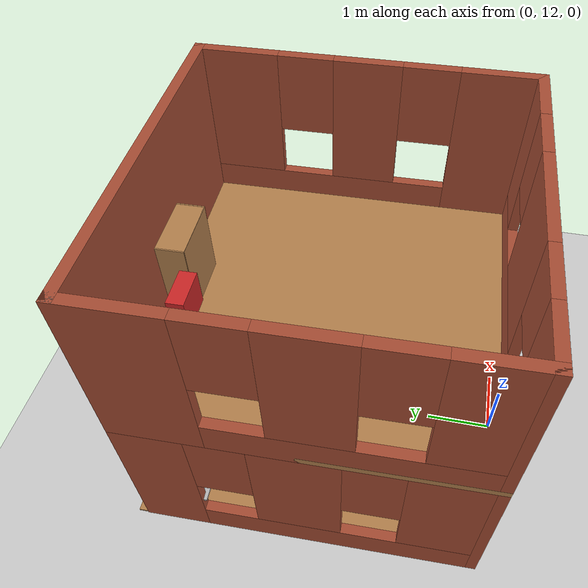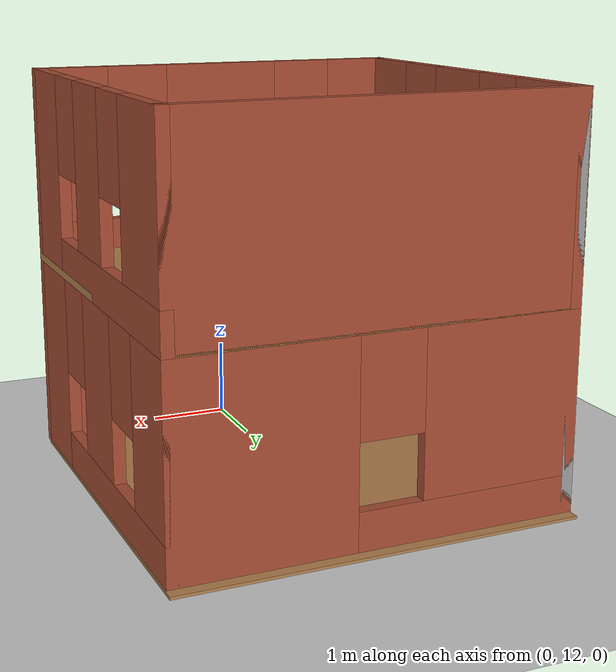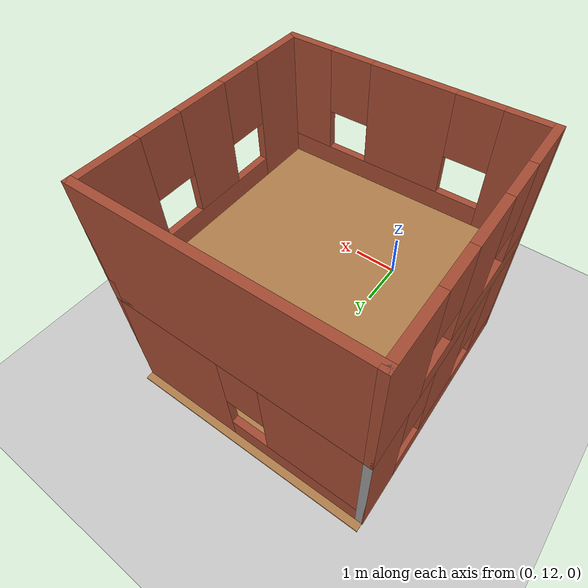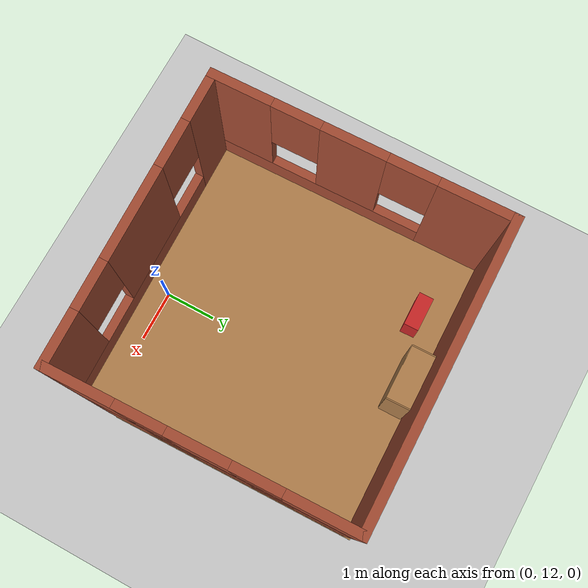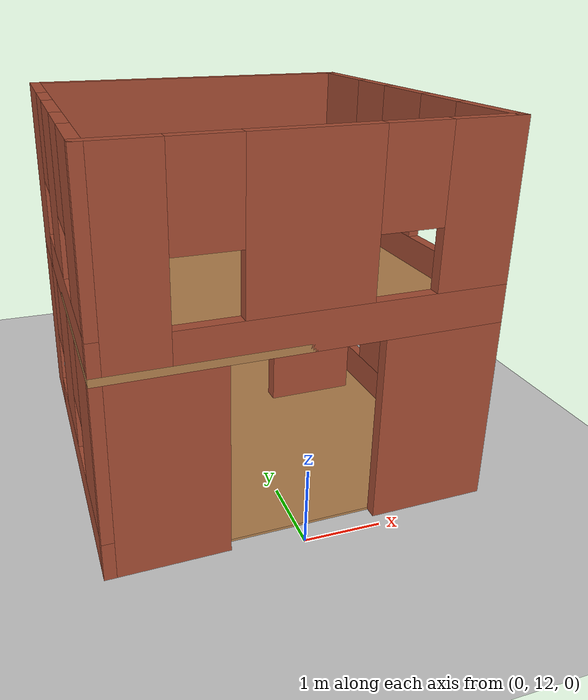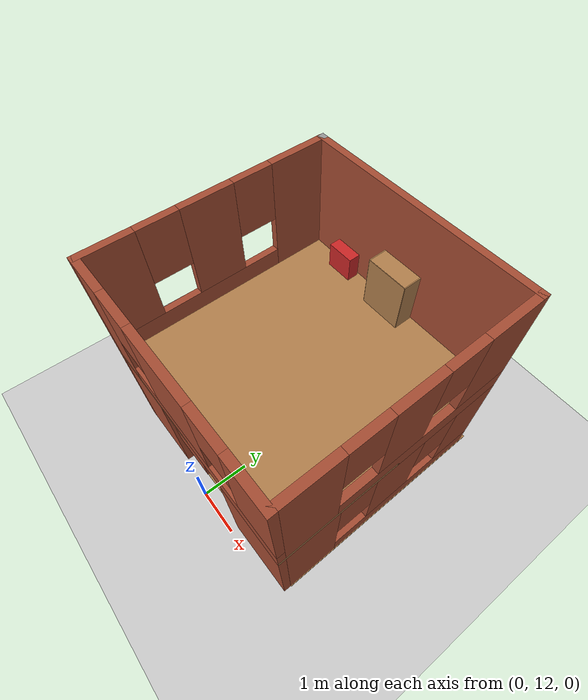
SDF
<sdf version="1.6">
 <world name="default">
  <light name="sun" type="directional">
   <pose>0 0 10 0 -0 0</pose>
   <diffuse>0.8 0.8 0.8 1</diffuse>
   <specular>0.2 0.2 0.2 1</specular>
   <attenuation>
    <range>1000</range>
    <constant>0.9</constant>
    <linear>0.01</linear>
    <quadratic>0.001</quadratic>
   </attenuation>
   <direction>-0.5 0.1 -0.9</direction>
  </light>
  <model name="ground_plane">
   <static>1</static>
   <link name="link">
    <collision name="collision">
     <geometry><plane><normal>0 0 1</normal><size>100 100</size></plane></geometry>
     <surface><friction><ode><mu>100</mu><mu2>50</mu2></ode></friction></surface>
    </collision>
    <visual name="visual">
     <cast_shadows>0</cast_shadows>
     <geometry><plane><normal>0 0 1</normal><size>100 100</size></plane></geometry>
     <material>
      <script><uri>file://media/materials/scripts/gazebo.material</uri><name>Gazebo/Grey</name></script>
     </material>
    </visual>
   </link>
  </model>
  <gravity>0 0 -9.8</gravity>
  <magnetic_field>6e-06 2.3e-05 -4.2e-05</magnetic_field>
  <atmosphere type="adiabatic"/>
  <physics name="default_physics" default="0" type="ode">
   <max_step_size>0.001</max_step_size>
   <real_time_factor>1</real_time_factor>
   <real_time_update_rate>1000</real_time_update_rate>
  </physics>
  <scene><ambient>0.4 0.4 0.4 1</ambient><background>0.7 0.7 0.7 1</background><shadows>1</shadows></scene>
  <spherical_coordinates>
   <surface_model>EARTH_WGS84</surface_model>
   <latitude_deg>0</latitude_deg>
   <longitude_deg>0</longitude_deg>
   <elevation>0</elevation>
   <heading_deg>0</heading_deg>
  </spherical_coordinates>
  <model name="building1">
   <link name="Floor_0">
    <pose>0 0 2.5 0 -0 0</pose>
    <inertial>
     <mass>1</mass>
     <inertia><ixx>1</ixx><ixy>0</ixy><ixz>0</ixz><iyy>1</iyy><iyz>0</iyz><izz>1</izz></inertia>
    </inertial>
    <visual name="Floor_0_Visual">
     <pose>0 0 0.05 0 -0 0</pose>
     <geometry><box><size>5 5 0.1</size></box></geometry>
     <material>
      <script><uri>file://media/materials/scripts/gazebo.material</uri><name>Gazebo/Wood</name></script>
      <ambient>1 1 1 1</ambient>
      <shader type="pixel"><normal_map>__default__</normal_map></shader>
     </material>
     <meta><layer>1</layer></meta>
    </visual>
    <collision name="Floor_0_Collision">
     <pose>0 0 0.05 0 -0 0</pose>
     <geometry><box><size>5 5 0.1</size></box></geometry>
     <surface>
      <friction>
       <ode><mu>1</mu><mu2>1</mu2><fdir1>0 0 0</fdir1><slip1>0</slip1><slip2>0</slip2></ode>
       <torsional>
        <coefficient>1</coefficient>
        <patch_radius>0</patch_radius>
        <surface_radius>0</surface_radius>
        <use_patch_radius>1</use_patch_radius>
        <ode><slip>0</slip></ode>
       </torsional>
      </friction>
      <bounce><restitution_coefficient>0</restitution_coefficient><threshold>1e+06</threshold></bounce>
      <contact>
       <collide_without_contact>0</collide_without_contact>
       <collide_without_contact_bitmask>1</collide_without_contact_bitmask>
       <collide_bitmask>1</collide_bitmask>
       <ode>
        <soft_cfm>0</soft_cfm>
        <soft_erp>0.2</soft_erp>
        <kp>1e+13</kp>
        <kd>1</kd>
        <max_vel>0.01</max_vel>
        <min_depth>0</min_depth>
       </ode>
       <bullet>
        <split_impulse>1</split_impulse>
        <split_impulse_penetration_threshold>-0.01</split_impulse_penetration_threshold>
        <soft_cfm>0</soft_cfm>
        <soft_erp>0.2</soft_erp>
        <kp>1e+13</kp>
        <kd>1</kd>
       </bullet>
      </contact>
     </surface>
    </collision>
   </link>
   <link name="Floor_0_clone">
    <pose>-0.013101 -0.148574 -0.075535 0 -0 0</pose>
    <gravity>0</gravity>
    <inertial>
     <mass>1</mass>
     <inertia><ixx>1</ixx><ixy>0</ixy><ixz>0</ixz><iyy>1</iyy><iyz>0</iyz><izz>1</izz></inertia>
    </inertial>
    <visual name="Floor_0_Visual">
     <pose>0 0 0.05 0 -0 0</pose>
     <geometry><box><size>5 5 0.1</size></box></geometry>
     <material>
      <script><uri>file://media/materials/scripts/gazebo.material</uri><name>Gazebo/Wood</name></script>
      <ambient>1 1 1 1</ambient>
      <shader type="pixel"><normal_map>__default__</normal_map></shader>
     </material>
     <meta><layer>1</layer></meta>
    </visual>
    <collision name="Floor_0_Collision">
     <pose>0 0 0.05 0 -0 0</pose>
     <geometry><box><size>5 5 0.1</size></box></geometry>
     <surface>
      <friction>
       <ode><mu>1</mu><mu2>1</mu2><fdir1>0 0 0</fdir1><slip1>0</slip1><slip2>0</slip2></ode>
       <torsional>
        <coefficient>1</coefficient>
        <patch_radius>0</patch_radius>
        <surface_radius>0</surface_radius>
        <use_patch_radius>1</use_patch_radius>
        <ode><slip>0</slip></ode>
       </torsional>
      </friction>
      <bounce><restitution_coefficient>0</restitution_coefficient><threshold>1e+06</threshold></bounce>
      <contact>
       <collide_without_contact>0</collide_without_contact>
       <collide_without_contact_bitmask>1</collide_without_contact_bitmask>
       <collide_bitmask>1</collide_bitmask>
       <ode>
        <soft_cfm>0</soft_cfm>
        <soft_erp>0.2</soft_erp>
        <kp>1e+13</kp>
        <kd>1</kd>
        <max_vel>0.01</max_vel>
        <min_depth>0</min_depth>
       </ode>
       <bullet>
        <split_impulse>1</split_impulse>
        <split_impulse_penetration_threshold>-0.01</split_impulse_penetration_threshold>
        <soft_cfm>0</soft_cfm>
        <soft_erp>0.2</soft_erp>
        <kp>1e+13</kp>
        <kd>1</kd>
       </bullet>
      </contact>
     </surface>
    </collision>
   </link>
   <link name="Wall_1">
    <pose>0 -2.425 0 0 -0 0</pose>
    <visual name="Wall_1_Visual_3">
     <pose>0.109106 0 1.9 0 -0 0</pose>
     <geometry><box><size>0.8 0.15 1.2</size></box></geometry>
     <material>
      <script><uri>file://media/materials/scripts/gazebo.material</uri><name>Gazebo/Bricks</name></script>
      <ambient>1 1 1 1</ambient>
      <shader type="pixel"/>
     </material>
     <meta><layer>0</layer></meta>
    </visual>
    <visual name="Wall_1_Visual_1">
     <pose>1.10455 0 0.25 0 -0 0</pose>
     <geometry><box><size>2.79089 0.15 0.5</size></box></geometry>
     <material>
      <script><uri>file://media/materials/scripts/gazebo.material</uri><name>Gazebo/Bricks</name></script>
      <ambient>1 1 1 1</ambient>
      <shader type="pixel"/>
     </material>
     <meta><layer>0</layer></meta>
    </visual>
    <visual name="Wall_1_Visual_2">
     <pose>1.50455 0 1.5 0 -0 0</pose>
     <geometry><box><size>1.99089 0.15 2</size></box></geometry>
     <material>
      <script><uri>file://media/materials/scripts/gazebo.material</uri><name>Gazebo/Bricks</name></script>
      <ambient>1 1 1 1</ambient>
      <shader type="pixel"/>
     </material>
     <meta><layer>0</layer></meta>
    </visual>
    <visual name="Wall_1_Visual_0">
     <pose>-1.39545 0 1.25 0 -0 0</pose>
     <geometry><box><size>2.20911 0.15 2.5</size></box></geometry>
     <material>
      <script><uri>file://media/materials/scripts/gazebo.material</uri><name>Gazebo/Bricks</name></script>
      <ambient>1 1 1 1</ambient>
      <shader type="pixel"/>
     </material>
     <meta><layer>0</layer></meta>
    </visual>
    <collision name="Wall_1_Collision_3">
     <pose>0.109106 0 1.9 0 -0 0</pose>
     <geometry><box><size>0.8 0.15 1.2</size></box></geometry>
     <surface>
      <friction>
       <ode><mu>1</mu><mu2>1</mu2><fdir1>0 0 0</fdir1><slip1>0</slip1><slip2>0</slip2></ode>
       <torsional>
        <coefficient>1</coefficient>
        <patch_radius>0</patch_radius>
        <surface_radius>0</surface_radius>
        <use_patch_radius>1</use_patch_radius>
        <ode><slip>0</slip></ode>
       </torsional>
      </friction>
      <bounce><restitution_coefficient>0</restitution_coefficient><threshold>1e+06</threshold></bounce>
      <contact>
       <collide_without_contact>0</collide_without_contact>
       <collide_without_contact_bitmask>1</collide_without_contact_bitmask>
       <collide_bitmask>1</collide_bitmask>
       <ode>
        <soft_cfm>0</soft_cfm>
        <soft_erp>0.2</soft_erp>
        <kp>1e+13</kp>
        <kd>1</kd>
        <max_vel>0.01</max_vel>
        <min_depth>0</min_depth>
       </ode>
       <bullet>
        <split_impulse>1</split_impulse>
        <split_impulse_penetration_threshold>-0.01</split_impulse_penetration_threshold>
        <soft_cfm>0</soft_cfm>
        <soft_erp>0.2</soft_erp>
        <kp>1e+13</kp>
        <kd>1</kd>
       </bullet>
      </contact>
     </surface>
    </collision>
    <collision name="Wall_1_Collision_2">
     <pose>1.50455 0 1.5 0 -0 0</pose>
     <geometry><box><size>1.99089 0.15 2</size></box></geometry>
     <surface>
      <friction>
       <ode><mu>1</mu><mu2>1</mu2><fdir1>0 0 0</fdir1><slip1>0</slip1><slip2>0</slip2></ode>
       <torsional>
        <coefficient>1</coefficient>
        <patch_radius>0</patch_radius>
        <surface_radius>0</surface_radius>
        <use_patch_radius>1</use_patch_radius>
        <ode><slip>0</slip></ode>
       </torsional>
      </friction>
      <bounce><restitution_coefficient>0</restitution_coefficient><threshold>1e+06</threshold></bounce>
      <contact>
       <collide_without_contact>0</collide_without_contact>
       <collide_without_contact_bitmask>1</collide_without_contact_bitmask>
       <collide_bitmask>1</collide_bitmask>
       <ode>
        <soft_cfm>0</soft_cfm>
        <soft_erp>0.2</soft_erp>
        <kp>1e+13</kp>
        <kd>1</kd>
        <max_vel>0.01</max_vel>
        <min_depth>0</min_depth>
       </ode>
       <bullet>
        <split_impulse>1</split_impulse>
        <split_impulse_penetration_threshold>-0.01</split_impulse_penetration_threshold>
        <soft_cfm>0</soft_cfm>
        <soft_erp>0.2</soft_erp>
        <kp>1e+13</kp>
        <kd>1</kd>
       </bullet>
      </contact>
     </surface>
    </collision>
    <collision name="Wall_1_Collision_1">
     <pose>1.10455 0 0.25 0 -0 0</pose>
     <geometry><box><size>2.79089 0.15 0.5</size></box></geometry>
     <surface>
      <friction>
       <ode><mu>1</mu><mu2>1</mu2><fdir1>0 0 0</fdir1><slip1>0</slip1><slip2>0</slip2></ode>
       <torsional>
        <coefficient>1</coefficient>
        <patch_radius>0</patch_radius>
        <surface_radius>0</surface_radius>
        <use_patch_radius>1</use_patch_radius>
        <ode><slip>0</slip></ode>
       </torsional>
      </friction>
      <bounce><restitution_coefficient>0</restitution_coefficient><threshold>1e+06</threshold></bounce>
      <contact>
       <collide_without_contact>0</collide_without_contact>
       <collide_without_contact_bitmask>1</collide_without_contact_bitmask>
       <collide_bitmask>1</collide_bitmask>
       <ode>
        <soft_cfm>0</soft_cfm>
        <soft_erp>0.2</soft_erp>
        <kp>1e+13</kp>
        <kd>1</kd>
        <max_vel>0.01</max_vel>
        <min_depth>0</min_depth>
       </ode>
       <bullet>
        <split_impulse>1</split_impulse>
        <split_impulse_penetration_threshold>-0.01</split_impulse_penetration_threshold>
        <soft_cfm>0</soft_cfm>
        <soft_erp>0.2</soft_erp>
        <kp>1e+13</kp>
        <kd>1</kd>
       </bullet>
      </contact>
     </surface>
    </collision>
    <collision name="Wall_1_Collision_0">
     <pose>-1.39545 0 1.25 0 -0 0</pose>
     <geometry><box><size>2.20911 0.15 2.5</size></box></geometry>
     <surface>
      <friction>
       <ode><mu>1</mu><mu2>1</mu2><fdir1>0 0 0</fdir1><slip1>0</slip1><slip2>0</slip2></ode>
       <torsional>
        <coefficient>1</coefficient>
        <patch_radius>0</patch_radius>
        <surface_radius>0</surface_radius>
        <use_patch_radius>1</use_patch_radius>
        <ode><slip>0</slip></ode>
       </torsional>
      </friction>
      <bounce><restitution_coefficient>0</restitution_coefficient><threshold>1e+06</threshold></bounce>
      <contact>
       <collide_without_contact>0</collide_without_contact>
       <collide_without_contact_bitmask>1</collide_without_contact_bitmask>
       <collide_bitmask>1</collide_bitmask>
       <ode>
        <soft_cfm>0</soft_cfm>
        <soft_erp>0.2</soft_erp>
        <kp>1e+13</kp>
        <kd>1</kd>
        <max_vel>0.01</max_vel>
        <min_depth>0</min_depth>
       </ode>
       <bullet>
        <split_impulse>1</split_impulse>
        <split_impulse_penetration_threshold>-0.01</split_impulse_penetration_threshold>
        <soft_cfm>0</soft_cfm>
        <soft_erp>0.2</soft_erp>
        <kp>1e+13</kp>
        <kd>1</kd>
       </bullet>
      </contact>
     </surface>
    </collision>
   </link>
   <link name="Wall_10">
    <pose>0 2.425 2.5 0 -0 3.14159</pose>
    <visual name="Wall_10_Visual_1">
     <pose>0.447808 0 0.25 0 -0 0</pose>
     <geometry><box><size>4.10438 0.15 0.5</size></box></geometry>
     <material>
      <script><uri>file://media/materials/scripts/gazebo.material</uri><name>Gazebo/Bricks</name></script>
      <ambient>1 1 1 1</ambient>
      <shader type="pixel"/>
     </material>
     <meta><layer>1</layer></meta>
    </visual>
    <visual name="Wall_10_Visual_5">
     <pose>1.14562 0 1.9 0 -0 0</pose>
     <geometry><box><size>0.8 0.15 1.2</size></box></geometry>
     <material>
      <script><uri>file://media/materials/scripts/gazebo.material</uri><name>Gazebo/Bricks</name></script>
      <ambient>1 1 1 1</ambient>
      <shader type="pixel"/>
     </material>
     <meta><layer>1</layer></meta>
    </visual>
    <visual name="Wall_10_Visual_0">
     <pose>-2.05219 0 1.25 0 -0 0</pose>
     <geometry><box><size>0.895617 0.15 2.5</size></box></geometry>
     <material>
      <script><uri>file://media/materials/scripts/gazebo.material</uri><name>Gazebo/Bricks</name></script>
      <ambient>1 1 1 1</ambient>
      <shader type="pixel"/>
     </material>
     <meta><layer>1</layer></meta>
    </visual>
    <visual name="Wall_10_Visual_3">
     <pose>2.02281 0 1.5 0 -0 0</pose>
     <geometry><box><size>0.954383 0.15 2</size></box></geometry>
     <material>
      <script><uri>file://media/materials/scripts/gazebo.material</uri><name>Gazebo/Bricks</name></script>
      <ambient>1 1 1 1</ambient>
      <shader type="pixel"/>
     </material>
     <meta><layer>1</layer></meta>
    </visual>
    <visual name="Wall_10_Visual_2">
     <pose>-0.029383 0 1.5 0 -0 0</pose>
     <geometry><box><size>1.55 0.15 2</size></box></geometry>
     <material>
      <script><uri>file://media/materials/scripts/gazebo.material</uri><name>Gazebo/Bricks</name></script>
      <ambient>1 1 1 1</ambient>
      <shader type="pixel"/>
     </material>
     <meta><layer>1</layer></meta>
    </visual>
    <visual name="Wall_10_Visual_4">
     <pose>-1.20438 0 1.9 0 -0 0</pose>
     <geometry><box><size>0.8 0.15 1.2</size></box></geometry>
     <material>
      <script><uri>file://media/materials/scripts/gazebo.material</uri><name>Gazebo/Bricks</name></script>
      <ambient>1 1 1 1</ambient>
      <shader type="pixel"/>
     </material>
     <meta><layer>1</layer></meta>
    </visual>
    <collision name="Wall_10_Collision_2">
     <pose>-0.029383 0 1.5 0 -0 0</pose>
     <geometry><box><size>1.55 0.15 2</size></box></geometry>
     <surface>
      <friction>
       <ode><mu>1</mu><mu2>1</mu2><fdir1>0 0 0</fdir1><slip1>0</slip1><slip2>0</slip2></ode>
       <torsional>
        <coefficient>1</coefficient>
        <patch_radius>0</patch_radius>
        <surface_radius>0</surface_radius>
        <use_patch_radius>1</use_patch_radius>
        <ode><slip>0</slip></ode>
       </torsional>
      </friction>
      <bounce><restitution_coefficient>0</restitution_coefficient><threshold>1e+06</threshold></bounce>
      <contact>
       <collide_without_contact>0</collide_without_contact>
       <collide_without_contact_bitmask>1</collide_without_contact_bitmask>
       <collide_bitmask>1</collide_bitmask>
       <ode>
        <soft_cfm>0</soft_cfm>
        <soft_erp>0.2</soft_erp>
        <kp>1e+13</kp>
        <kd>1</kd>
        <max_vel>0.01</max_vel>
        <min_depth>0</min_depth>
       </ode>
       <bullet>
        <split_impulse>1</split_impulse>
        <split_impulse_penetration_threshold>-0.01</split_impulse_penetration_threshold>
        <soft_cfm>0</soft_cfm>
        <soft_erp>0.2</soft_erp>
        <kp>1e+13</kp>
        <kd>1</kd>
       </bullet>
      </contact>
     </surface>
    </collision>
    <collision name="Wall_10_Collision_1">
     <pose>0.447808 0 0.25 0 -0 0</pose>
     <geometry><box><size>4.10438 0.15 0.5</size></box></geometry>
     <surface>
      <friction>
       <ode><mu>1</mu><mu2>1</mu2><fdir1>0 0 0</fdir1><slip1>0</slip1><slip2>0</slip2></ode>
       <torsional>
        <coefficient>1</coefficient>
        <patch_radius>0</patch_radius>
        <surface_radius>0</surface_radius>
        <use_patch_radius>1</use_patch_radius>
        <ode><slip>0</slip></ode>
       </torsional>
      </friction>
      <bounce><restitution_coefficient>0</restitution_coefficient><threshold>1e+06</threshold></bounce>
      <contact>
       <collide_without_contact>0</collide_without_contact>
       <collide_without_contact_bitmask>1</collide_without_contact_bitmask>
       <collide_bitmask>1</collide_bitmask>
       <ode>
        <soft_cfm>0</soft_cfm>
        <soft_erp>0.2</soft_erp>
        <kp>1e+13</kp>
        <kd>1</kd>
        <max_vel>0.01</max_vel>
        <min_depth>0</min_depth>
       </ode>
       <bullet>
        <split_impulse>1</split_impulse>
        <split_impulse_penetration_threshold>-0.01</split_impulse_penetration_threshold>
        <soft_cfm>0</soft_cfm>
        <soft_erp>0.2</soft_erp>
        <kp>1e+13</kp>
        <kd>1</kd>
       </bullet>
      </contact>
     </surface>
    </collision>
    <collision name="Wall_10_Collision_5">
     <pose>1.14562 0 1.9 0 -0 0</pose>
     <geometry><box><size>0.8 0.15 1.2</size></box></geometry>
     <surface>
      <friction>
       <ode><mu>1</mu><mu2>1</mu2><fdir1>0 0 0</fdir1><slip1>0</slip1><slip2>0</slip2></ode>
       <torsional>
        <coefficient>1</coefficient>
        <patch_radius>0</patch_radius>
        <surface_radius>0</surface_radius>
        <use_patch_radius>1</use_patch_radius>
        <ode><slip>0</slip></ode>
       </torsional>
      </friction>
      <bounce><restitution_coefficient>0</restitution_coefficient><threshold>1e+06</threshold></bounce>
      <contact>
       <collide_without_contact>0</collide_without_contact>
       <collide_without_contact_bitmask>1</collide_without_contact_bitmask>
       <collide_bitmask>1</collide_bitmask>
       <ode>
        <soft_cfm>0</soft_cfm>
        <soft_erp>0.2</soft_erp>
        <kp>1e+13</kp>
        <kd>1</kd>
        <max_vel>0.01</max_vel>
        <min_depth>0</min_depth>
       </ode>
       <bullet>
        <split_impulse>1</split_impulse>
        <split_impulse_penetration_threshold>-0.01</split_impulse_penetration_threshold>
        <soft_cfm>0</soft_cfm>
        <soft_erp>0.2</soft_erp>
        <kp>1e+13</kp>
        <kd>1</kd>
       </bullet>
      </contact>
     </surface>
    </collision>
    <collision name="Wall_10_Collision_0">
     <pose>-2.05219 0 1.25 0 -0 0</pose>
     <geometry><box><size>0.895617 0.15 2.5</size></box></geometry>
     <surface>
      <friction>
       <ode><mu>1</mu><mu2>1</mu2><fdir1>0 0 0</fdir1><slip1>0</slip1><slip2>0</slip2></ode>
       <torsional>
        <coefficient>1</coefficient>
        <patch_radius>0</patch_radius>
        <surface_radius>0</surface_radius>
        <use_patch_radius>1</use_patch_radius>
        <ode><slip>0</slip></ode>
       </torsional>
      </friction>
      <bounce><restitution_coefficient>0</restitution_coefficient><threshold>1e+06</threshold></bounce>
      <contact>
       <collide_without_contact>0</collide_without_contact>
       <collide_without_contact_bitmask>1</collide_without_contact_bitmask>
       <collide_bitmask>1</collide_bitmask>
       <ode>
        <soft_cfm>0</soft_cfm>
        <soft_erp>0.2</soft_erp>
        <kp>1e+13</kp>
        <kd>1</kd>
        <max_vel>0.01</max_vel>
        <min_depth>0</min_depth>
       </ode>
       <bullet>
        <split_impulse>1</split_impulse>
        <split_impulse_penetration_threshold>-0.01</split_impulse_penetration_threshold>
        <soft_cfm>0</soft_cfm>
        <soft_erp>0.2</soft_erp>
        <kp>1e+13</kp>
        <kd>1</kd>
       </bullet>
      </contact>
     </surface>
    </collision>
    <collision name="Wall_10_Collision_4">
     <pose>-1.20438 0 1.9 0 -0 0</pose>
     <geometry><box><size>0.8 0.15 1.2</size></box></geometry>
     <surface>
      <friction>
       <ode><mu>1</mu><mu2>1</mu2><fdir1>0 0 0</fdir1><slip1>0</slip1><slip2>0</slip2></ode>
       <torsional>
        <coefficient>1</coefficient>
        <patch_radius>0</patch_radius>
        <surface_radius>0</surface_radius>
        <use_patch_radius>1</use_patch_radius>
        <ode><slip>0</slip></ode>
       </torsional>
      </friction>
      <bounce><restitution_coefficient>0</restitution_coefficient><threshold>1e+06</threshold></bounce>
      <contact>
       <collide_without_contact>0</collide_without_contact>
       <collide_without_contact_bitmask>1</collide_without_contact_bitmask>
       <collide_bitmask>1</collide_bitmask>
       <ode>
        <soft_cfm>0</soft_cfm>
        <soft_erp>0.2</soft_erp>
        <kp>1e+13</kp>
        <kd>1</kd>
        <max_vel>0.01</max_vel>
        <min_depth>0</min_depth>
       </ode>
       <bullet>
        <split_impulse>1</split_impulse>
        <split_impulse_penetration_threshold>-0.01</split_impulse_penetration_threshold>
        <soft_cfm>0</soft_cfm>
        <soft_erp>0.2</soft_erp>
        <kp>1e+13</kp>
        <kd>1</kd>
       </bullet>
      </contact>
     </surface>
    </collision>
    <collision name="Wall_10_Collision_3">
     <pose>2.02281 0 1.5 0 -0 0</pose>
     <geometry><box><size>0.954383 0.15 2</size></box></geometry>
     <surface>
      <friction>
       <ode><mu>1</mu><mu2>1</mu2><fdir1>0 0 0</fdir1><slip1>0</slip1><slip2>0</slip2></ode>
       <torsional>
        <coefficient>1</coefficient>
        <patch_radius>0</patch_radius>
        <surface_radius>0</surface_radius>
        <use_patch_radius>1</use_patch_radius>
        <ode><slip>0</slip></ode>
       </torsional>
      </friction>
      <bounce><restitution_coefficient>0</restitution_coefficient><threshold>1e+06</threshold></bounce>
      <contact>
       <collide_without_contact>0</collide_without_contact>
       <collide_without_contact_bitmask>1</collide_without_contact_bitmask>
       <collide_bitmask>1</collide_bitmask>
       <ode>
        <soft_cfm>0</soft_cfm>
        <soft_erp>0.2</soft_erp>
        <kp>1e+13</kp>
        <kd>1</kd>
        <max_vel>0.01</max_vel>
        <min_depth>0</min_depth>
       </ode>
       <bullet>
        <split_impulse>1</split_impulse>
        <split_impulse_penetration_threshold>-0.01</split_impulse_penetration_threshold>
        <soft_cfm>0</soft_cfm>
        <soft_erp>0.2</soft_erp>
        <kp>1e+13</kp>
        <kd>1</kd>
       </bullet>
      </contact>
     </surface>
    </collision>
   </link>
   <link name="Wall_11">
    <pose>-2.425 0 2.5 0 0 -1.5708</pose>
    <visual name="Wall_11_Visual_0">
     <pose>-1.91127 0 1.25 0 -0 0</pose>
     <geometry><box><size>1.17746 0.15 2.5</size></box></geometry>
     <material>
      <script><uri>file://media/materials/scripts/gazebo.material</uri><name>Gazebo/Bricks</name></script>
      <ambient>1 1 1 1</ambient>
      <shader type="pixel"/>
     </material>
     <meta><layer>1</layer></meta>
    </visual>
    <visual name="Wall_11_Visual_4">
     <pose>-0.922536 0 1.9 0 -0 0</pose>
     <geometry><box><size>0.8 0.15 1.2</size></box></geometry>
     <material>
      <script><uri>file://media/materials/scripts/gazebo.material</uri><name>Gazebo/Bricks</name></script>
      <ambient>1 1 1 1</ambient>
      <shader type="pixel"/>
     </material>
     <meta><layer>1</layer></meta>
    </visual>
    <visual name="Wall_11_Visual_1">
     <pose>0.588732 0 0.25 0 -0 0</pose>
     <geometry><box><size>3.82254 0.15 0.5</size></box></geometry>
     <material>
      <script><uri>file://media/materials/scripts/gazebo.material</uri><name>Gazebo/Bricks</name></script>
      <ambient>1 1 1 1</ambient>
      <shader type="pixel"/>
     </material>
     <meta><layer>1</layer></meta>
    </visual>
    <visual name="Wall_11_Visual_5">
     <pose>0.857464 0 1.9 0 -0 0</pose>
     <geometry><box><size>0.8 0.15 1.2</size></box></geometry>
     <material>
      <script><uri>file://media/materials/scripts/gazebo.material</uri><name>Gazebo/Bricks</name></script>
      <ambient>1 1 1 1</ambient>
      <shader type="pixel"/>
     </material>
     <meta><layer>1</layer></meta>
    </visual>
    <visual name="Wall_11_Visual_3">
     <pose>1.87873 0 1.5 0 -0 0</pose>
     <geometry><box><size>1.24254 0.15 2</size></box></geometry>
     <material>
      <script><uri>file://media/materials/scripts/gazebo.material</uri><name>Gazebo/Bricks</name></script>
      <ambient>1 1 1 1</ambient>
      <shader type="pixel"/>
     </material>
     <meta><layer>1</layer></meta>
    </visual>
    <visual name="Wall_11_Visual_2">
     <pose>-0.032536 0 1.5 0 -0 0</pose>
     <geometry><box><size>0.98 0.15 2</size></box></geometry>
     <material>
      <script><uri>file://media/materials/scripts/gazebo.material</uri><name>Gazebo/Bricks</name></script>
      <ambient>1 1 1 1</ambient>
      <shader type="pixel"/>
     </material>
     <meta><layer>1</layer></meta>
    </visual>
    <collision name="Wall_11_Collision_5">
     <pose>0.857464 0 1.9 0 -0 0</pose>
     <geometry><box><size>0.8 0.15 1.2</size></box></geometry>
     <surface>
      <friction>
       <ode><mu>1</mu><mu2>1</mu2><fdir1>0 0 0</fdir1><slip1>0</slip1><slip2>0</slip2></ode>
       <torsional>
        <coefficient>1</coefficient>
        <patch_radius>0</patch_radius>
        <surface_radius>0</surface_radius>
        <use_patch_radius>1</use_patch_radius>
        <ode><slip>0</slip></ode>
       </torsional>
      </friction>
      <bounce><restitution_coefficient>0</restitution_coefficient><threshold>1e+06</threshold></bounce>
      <contact>
       <collide_without_contact>0</collide_without_contact>
       <collide_without_contact_bitmask>1</collide_without_contact_bitmask>
       <collide_bitmask>1</collide_bitmask>
       <ode>
        <soft_cfm>0</soft_cfm>
        <soft_erp>0.2</soft_erp>
        <kp>1e+13</kp>
        <kd>1</kd>
        <max_vel>0.01</max_vel>
        <min_depth>0</min_depth>
       </ode>
       <bullet>
        <split_impulse>1</split_impulse>
        <split_impulse_penetration_threshold>-0.01</split_impulse_penetration_threshold>
        <soft_cfm>0</soft_cfm>
        <soft_erp>0.2</soft_erp>
        <kp>1e+13</kp>
        <kd>1</kd>
       </bullet>
      </contact>
     </surface>
    </collision>
    <collision name="Wall_11_Collision_4">
     <pose>-0.922536 0 1.9 0 -0 0</pose>
     <geometry><box><size>0.8 0.15 1.2</size></box></geometry>
     <surface>
      <friction>
       <ode><mu>1</mu><mu2>1</mu2><fdir1>0 0 0</fdir1><slip1>0</slip1><slip2>0</slip2></ode>
       <torsional>
        <coefficient>1</coefficient>
        <patch_radius>0</patch_radius>
        <surface_radius>0</surface_radius>
        <use_patch_radius>1</use_patch_radius>
        <ode><slip>0</slip></ode>
       </torsional>
      </friction>
      <bounce><restitution_coefficient>0</restitution_coefficient><threshold>1e+06</threshold></bounce>
      <contact>
       <collide_without_contact>0</collide_without_contact>
       <collide_without_contact_bitmask>1</collide_without_contact_bitmask>
       <collide_bitmask>1</collide_bitmask>
       <ode>
        <soft_cfm>0</soft_cfm>
        <soft_erp>0.2</soft_erp>
        <kp>1e+13</kp>
        <kd>1</kd>
        <max_vel>0.01</max_vel>
        <min_depth>0</min_depth>
       </ode>
       <bullet>
        <split_impulse>1</split_impulse>
        <split_impulse_penetration_threshold>-0.01</split_impulse_penetration_threshold>
        <soft_cfm>0</soft_cfm>
        <soft_erp>0.2</soft_erp>
        <kp>1e+13</kp>
        <kd>1</kd>
       </bullet>
      </contact>
     </surface>
    </collision>
    <collision name="Wall_11_Collision_2">
     <pose>-0.032536 0 1.5 0 -0 0</pose>
     <geometry><box><size>0.98 0.15 2</size></box></geometry>
     <surface>
      <friction>
       <ode><mu>1</mu><mu2>1</mu2><fdir1>0 0 0</fdir1><slip1>0</slip1><slip2>0</slip2></ode>
       <torsional>
        <coefficient>1</coefficient>
        <patch_radius>0</patch_radius>
        <surface_radius>0</surface_radius>
        <use_patch_radius>1</use_patch_radius>
        <ode><slip>0</slip></ode>
       </torsional>
      </friction>
      <bounce><restitution_coefficient>0</restitution_coefficient><threshold>1e+06</threshold></bounce>
      <contact>
       <collide_without_contact>0</collide_without_contact>
       <collide_without_contact_bitmask>1</collide_without_contact_bitmask>
       <collide_bitmask>1</collide_bitmask>
       <ode>
        <soft_cfm>0</soft_cfm>
        <soft_erp>0.2</soft_erp>
        <kp>1e+13</kp>
        <kd>1</kd>
        <max_vel>0.01</max_vel>
        <min_depth>0</min_depth>
       </ode>
       <bullet>
        <split_impulse>1</split_impulse>
        <split_impulse_penetration_threshold>-0.01</split_impulse_penetration_threshold>
        <soft_cfm>0</soft_cfm>
        <soft_erp>0.2</soft_erp>
        <kp>1e+13</kp>
        <kd>1</kd>
       </bullet>
      </contact>
     </surface>
    </collision>
    <collision name="Wall_11_Collision_3">
     <pose>1.87873 0 1.5 0 -0 0</pose>
     <geometry><box><size>1.24254 0.15 2</size></box></geometry>
     <surface>
      <friction>
       <ode><mu>1</mu><mu2>1</mu2><fdir1>0 0 0</fdir1><slip1>0</slip1><slip2>0</slip2></ode>
       <torsional>
        <coefficient>1</coefficient>
        <patch_radius>0</patch_radius>
        <surface_radius>0</surface_radius>
        <use_patch_radius>1</use_patch_radius>
        <ode><slip>0</slip></ode>
       </torsional>
      </friction>
      <bounce><restitution_coefficient>0</restitution_coefficient><threshold>1e+06</threshold></bounce>
      <contact>
       <collide_without_contact>0</collide_without_contact>
       <collide_without_contact_bitmask>1</collide_without_contact_bitmask>
       <collide_bitmask>1</collide_bitmask>
       <ode>
        <soft_cfm>0</soft_cfm>
        <soft_erp>0.2</soft_erp>
        <kp>1e+13</kp>
        <kd>1</kd>
        <max_vel>0.01</max_vel>
        <min_depth>0</min_depth>
       </ode>
       <bullet>
        <split_impulse>1</split_impulse>
        <split_impulse_penetration_threshold>-0.01</split_impulse_penetration_threshold>
        <soft_cfm>0</soft_cfm>
        <soft_erp>0.2</soft_erp>
        <kp>1e+13</kp>
        <kd>1</kd>
       </bullet>
      </contact>
     </surface>
    </collision>
    <collision name="Wall_11_Collision_0">
     <pose>-1.91127 0 1.25 0 -0 0</pose>
     <geometry><box><size>1.17746 0.15 2.5</size></box></geometry>
     <surface>
      <friction>
       <ode><mu>1</mu><mu2>1</mu2><fdir1>0 0 0</fdir1><slip1>0</slip1><slip2>0</slip2></ode>
       <torsional>
        <coefficient>1</coefficient>
        <patch_radius>0</patch_radius>
        <surface_radius>0</surface_radius>
        <use_patch_radius>1</use_patch_radius>
        <ode><slip>0</slip></ode>
       </torsional>
      </friction>
      <bounce><restitution_coefficient>0</restitution_coefficient><threshold>1e+06</threshold></bounce>
      <contact>
       <collide_without_contact>0</collide_without_contact>
       <collide_without_contact_bitmask>1</collide_without_contact_bitmask>
       <collide_bitmask>1</collide_bitmask>
       <ode>
        <soft_cfm>0</soft_cfm>
        <soft_erp>0.2</soft_erp>
        <kp>1e+13</kp>
        <kd>1</kd>
        <max_vel>0.01</max_vel>
        <min_depth>0</min_depth>
       </ode>
       <bullet>
        <split_impulse>1</split_impulse>
        <split_impulse_penetration_threshold>-0.01</split_impulse_penetration_threshold>
        <soft_cfm>0</soft_cfm>
        <soft_erp>0.2</soft_erp>
        <kp>1e+13</kp>
        <kd>1</kd>
       </bullet>
      </contact>
     </surface>
    </collision>
    <collision name="Wall_11_Collision_1">
     <pose>0.588732 0 0.25 0 -0 0</pose>
     <geometry><box><size>3.82254 0.15 0.5</size></box></geometry>
     <surface>
      <friction>
       <ode><mu>1</mu><mu2>1</mu2><fdir1>0 0 0</fdir1><slip1>0</slip1><slip2>0</slip2></ode>
       <torsional>
        <coefficient>1</coefficient>
        <patch_radius>0</patch_radius>
        <surface_radius>0</surface_radius>
        <use_patch_radius>1</use_patch_radius>
        <ode><slip>0</slip></ode>
       </torsional>
      </friction>
      <bounce><restitution_coefficient>0</restitution_coefficient><threshold>1e+06</threshold></bounce>
      <contact>
       <collide_without_contact>0</collide_without_contact>
       <collide_without_contact_bitmask>1</collide_without_contact_bitmask>
       <collide_bitmask>1</collide_bitmask>
       <ode>
        <soft_cfm>0</soft_cfm>
        <soft_erp>0.2</soft_erp>
        <kp>1e+13</kp>
        <kd>1</kd>
        <max_vel>0.01</max_vel>
        <min_depth>0</min_depth>
       </ode>
       <bullet>
        <split_impulse>1</split_impulse>
        <split_impulse_penetration_threshold>-0.01</split_impulse_penetration_threshold>
        <soft_cfm>0</soft_cfm>
        <soft_erp>0.2</soft_erp>
        <kp>1e+13</kp>
        <kd>1</kd>
       </bullet>
      </contact>
     </surface>
    </collision>
   </link>
   <link name="Wall_2">
    <pose>2.425 -2.425 0 0 -0 0</pose>
    <visual name="Wall_2_Visual">
     <pose>0 0 1.25 0 -0 0</pose>
     <geometry><box><size>0.15 0.15 2.5</size></box></geometry>
     <material>
      <script><uri>file://media/materials/scripts/gazebo.material</uri><name>Gazebo/Grey</name></script>
      <ambient>1 1 1 1</ambient>
      <shader type="pixel"/>
     </material>
     <meta><layer>0</layer></meta>
    </visual>
    <collision name="Wall_2_Collision">
     <pose>0 0 1.25 0 -0 0</pose>
     <geometry><box><size>0.15 0.15 2.5</size></box></geometry>
     <surface>
      <friction>
       <ode><mu>1</mu><mu2>1</mu2><fdir1>0 0 0</fdir1><slip1>0</slip1><slip2>0</slip2></ode>
       <torsional>
        <coefficient>1</coefficient>
        <patch_radius>0</patch_radius>
        <surface_radius>0</surface_radius>
        <use_patch_radius>1</use_patch_radius>
        <ode><slip>0</slip></ode>
       </torsional>
      </friction>
      <bounce><restitution_coefficient>0</restitution_coefficient><threshold>1e+06</threshold></bounce>
      <contact>
       <collide_without_contact>0</collide_without_contact>
       <collide_without_contact_bitmask>1</collide_without_contact_bitmask>
       <collide_bitmask>1</collide_bitmask>
       <ode>
        <soft_cfm>0</soft_cfm>
        <soft_erp>0.2</soft_erp>
        <kp>1e+13</kp>
        <kd>1</kd>
        <max_vel>0.01</max_vel>
        <min_depth>0</min_depth>
       </ode>
       <bullet>
        <split_impulse>1</split_impulse>
        <split_impulse_penetration_threshold>-0.01</split_impulse_penetration_threshold>
        <soft_cfm>0</soft_cfm>
        <soft_erp>0.2</soft_erp>
        <kp>1e+13</kp>
        <kd>1</kd>
       </bullet>
      </contact>
     </surface>
    </collision>
   </link>
   <link name="Wall_3">
    <pose>2.425 0 0 0 -0 1.5708</pose>
    <visual name="Wall_3_Visual_4">
     <pose>-1.11345 0 1.9 0 -0 0</pose>
     <geometry><box><size>0.8 0.15 1.2</size></box></geometry>
     <material>
      <script><uri>file://media/materials/scripts/gazebo.material</uri><name>Gazebo/Bricks</name></script>
      <ambient>1 1 1 1</ambient>
      <shader type="pixel"/>
     </material>
     <meta><layer>0</layer></meta>
    </visual>
    <visual name="Wall_3_Visual_2">
     <pose>-0.109669 0 1.5 0 -0 0</pose>
     <geometry><box><size>1.20755 0.15 2</size></box></geometry>
     <material>
      <script><uri>file://media/materials/scripts/gazebo.material</uri><name>Gazebo/Bricks</name></script>
      <ambient>1 1 1 1</ambient>
      <shader type="pixel"/>
     </material>
     <meta><layer>0</layer></meta>
    </visual>
    <visual name="Wall_3_Visual_1">
     <pose>0.493277 0 0.25 0 -0 0</pose>
     <geometry><box><size>4.01345 0.15 0.5</size></box></geometry>
     <material>
      <script><uri>file://media/materials/scripts/gazebo.material</uri><name>Gazebo/Bricks</name></script>
      <ambient>1 1 1 1</ambient>
      <shader type="pixel"/>
     </material>
     <meta><layer>0</layer></meta>
    </visual>
    <visual name="Wall_3_Visual_5">
     <pose>0.894108 0 1.9 0 -0 0</pose>
     <geometry><box><size>0.8 0.15 1.2</size></box></geometry>
     <material>
      <script><uri>file://media/materials/scripts/gazebo.material</uri><name>Gazebo/Bricks</name></script>
      <ambient>1 1 1 1</ambient>
      <shader type="pixel"/>
     </material>
     <meta><layer>0</layer></meta>
    </visual>
    <visual name="Wall_3_Visual_0">
     <pose>-2.00672 0 1.25 0 -0 0</pose>
     <geometry><box><size>0.986553 0.15 2.5</size></box></geometry>
     <material>
      <script><uri>file://media/materials/scripts/gazebo.material</uri><name>Gazebo/Bricks</name></script>
      <ambient>1 1 1 1</ambient>
      <shader type="pixel"/>
     </material>
     <meta><layer>0</layer></meta>
    </visual>
    <visual name="Wall_3_Visual_3">
     <pose>1.89705 0 1.5 0 -0 0</pose>
     <geometry><box><size>1.20589 0.15 2</size></box></geometry>
     <material>
      <script><uri>file://media/materials/scripts/gazebo.material</uri><name>Gazebo/Bricks</name></script>
      <ambient>1 1 1 1</ambient>
      <shader type="pixel"/>
     </material>
     <meta><layer>0</layer></meta>
    </visual>
    <collision name="Wall_3_Collision_3">
     <pose>1.89705 0 1.5 0 -0 0</pose>
     <geometry><box><size>1.20589 0.15 2</size></box></geometry>
     <surface>
      <friction>
       <ode><mu>1</mu><mu2>1</mu2><fdir1>0 0 0</fdir1><slip1>0</slip1><slip2>0</slip2></ode>
       <torsional>
        <coefficient>1</coefficient>
        <patch_radius>0</patch_radius>
        <surface_radius>0</surface_radius>
        <use_patch_radius>1</use_patch_radius>
        <ode><slip>0</slip></ode>
       </torsional>
      </friction>
      <bounce><restitution_coefficient>0</restitution_coefficient><threshold>1e+06</threshold></bounce>
      <contact>
       <collide_without_contact>0</collide_without_contact>
       <collide_without_contact_bitmask>1</collide_without_contact_bitmask>
       <collide_bitmask>1</collide_bitmask>
       <ode>
        <soft_cfm>0</soft_cfm>
        <soft_erp>0.2</soft_erp>
        <kp>1e+13</kp>
        <kd>1</kd>
        <max_vel>0.01</max_vel>
        <min_depth>0</min_depth>
       </ode>
       <bullet>
        <split_impulse>1</split_impulse>
        <split_impulse_penetration_threshold>-0.01</split_impulse_penetration_threshold>
        <soft_cfm>0</soft_cfm>
        <soft_erp>0.2</soft_erp>
        <kp>1e+13</kp>
        <kd>1</kd>
       </bullet>
      </contact>
     </surface>
    </collision>
    <collision name="Wall_3_Collision_1">
     <pose>0.493277 0 0.25 0 -0 0</pose>
     <geometry><box><size>4.01345 0.15 0.5</size></box></geometry>
     <surface>
      <friction>
       <ode><mu>1</mu><mu2>1</mu2><fdir1>0 0 0</fdir1><slip1>0</slip1><slip2>0</slip2></ode>
       <torsional>
        <coefficient>1</coefficient>
        <patch_radius>0</patch_radius>
        <surface_radius>0</surface_radius>
        <use_patch_radius>1</use_patch_radius>
        <ode><slip>0</slip></ode>
       </torsional>
      </friction>
      <bounce><restitution_coefficient>0</restitution_coefficient><threshold>1e+06</threshold></bounce>
      <contact>
       <collide_without_contact>0</collide_without_contact>
       <collide_without_contact_bitmask>1</collide_without_contact_bitmask>
       <collide_bitmask>1</collide_bitmask>
       <ode>
        <soft_cfm>0</soft_cfm>
        <soft_erp>0.2</soft_erp>
        <kp>1e+13</kp>
        <kd>1</kd>
        <max_vel>0.01</max_vel>
        <min_depth>0</min_depth>
       </ode>
       <bullet>
        <split_impulse>1</split_impulse>
        <split_impulse_penetration_threshold>-0.01</split_impulse_penetration_threshold>
        <soft_cfm>0</soft_cfm>
        <soft_erp>0.2</soft_erp>
        <kp>1e+13</kp>
        <kd>1</kd>
       </bullet>
      </contact>
     </surface>
    </collision>
    <collision name="Wall_3_Collision_4">
     <pose>-1.11345 0 1.9 0 -0 0</pose>
     <geometry><box><size>0.8 0.15 1.2</size></box></geometry>
     <surface>
      <friction>
       <ode><mu>1</mu><mu2>1</mu2><fdir1>0 0 0</fdir1><slip1>0</slip1><slip2>0</slip2></ode>
       <torsional>
        <coefficient>1</coefficient>
        <patch_radius>0</patch_radius>
        <surface_radius>0</surface_radius>
        <use_patch_radius>1</use_patch_radius>
        <ode><slip>0</slip></ode>
       </torsional>
      </friction>
      <bounce><restitution_coefficient>0</restitution_coefficient><threshold>1e+06</threshold></bounce>
      <contact>
       <collide_without_contact>0</collide_without_contact>
       <collide_without_contact_bitmask>1</collide_without_contact_bitmask>
       <collide_bitmask>1</collide_bitmask>
       <ode>
        <soft_cfm>0</soft_cfm>
        <soft_erp>0.2</soft_erp>
        <kp>1e+13</kp>
        <kd>1</kd>
        <max_vel>0.01</max_vel>
        <min_depth>0</min_depth>
       </ode>
       <bullet>
        <split_impulse>1</split_impulse>
        <split_impulse_penetration_threshold>-0.01</split_impulse_penetration_threshold>
        <soft_cfm>0</soft_cfm>
        <soft_erp>0.2</soft_erp>
        <kp>1e+13</kp>
        <kd>1</kd>
       </bullet>
      </contact>
     </surface>
    </collision>
    <collision name="Wall_3_Collision_5">
     <pose>0.894108 0 1.9 0 -0 0</pose>
     <geometry><box><size>0.8 0.15 1.2</size></box></geometry>
     <surface>
      <friction>
       <ode><mu>1</mu><mu2>1</mu2><fdir1>0 0 0</fdir1><slip1>0</slip1><slip2>0</slip2></ode>
       <torsional>
        <coefficient>1</coefficient>
        <patch_radius>0</patch_radius>
        <surface_radius>0</surface_radius>
        <use_patch_radius>1</use_patch_radius>
        <ode><slip>0</slip></ode>
       </torsional>
      </friction>
      <bounce><restitution_coefficient>0</restitution_coefficient><threshold>1e+06</threshold></bounce>
      <contact>
       <collide_without_contact>0</collide_without_contact>
       <collide_without_contact_bitmask>1</collide_without_contact_bitmask>
       <collide_bitmask>1</collide_bitmask>
       <ode>
        <soft_cfm>0</soft_cfm>
        <soft_erp>0.2</soft_erp>
        <kp>1e+13</kp>
        <kd>1</kd>
        <max_vel>0.01</max_vel>
        <min_depth>0</min_depth>
       </ode>
       <bullet>
        <split_impulse>1</split_impulse>
        <split_impulse_penetration_threshold>-0.01</split_impulse_penetration_threshold>
        <soft_cfm>0</soft_cfm>
        <soft_erp>0.2</soft_erp>
        <kp>1e+13</kp>
        <kd>1</kd>
       </bullet>
      </contact>
     </surface>
    </collision>
    <collision name="Wall_3_Collision_2">
     <pose>-0.109669 0 1.5 0 -0 0</pose>
     <geometry><box><size>1.20755 0.15 2</size></box></geometry>
     <surface>
      <friction>
       <ode><mu>1</mu><mu2>1</mu2><fdir1>0 0 0</fdir1><slip1>0</slip1><slip2>0</slip2></ode>
       <torsional>
        <coefficient>1</coefficient>
        <patch_radius>0</patch_radius>
        <surface_radius>0</surface_radius>
        <use_patch_radius>1</use_patch_radius>
        <ode><slip>0</slip></ode>
       </torsional>
      </friction>
      <bounce><restitution_coefficient>0</restitution_coefficient><threshold>1e+06</threshold></bounce>
      <contact>
       <collide_without_contact>0</collide_without_contact>
       <collide_without_contact_bitmask>1</collide_without_contact_bitmask>
       <collide_bitmask>1</collide_bitmask>
       <ode>
        <soft_cfm>0</soft_cfm>
        <soft_erp>0.2</soft_erp>
        <kp>1e+13</kp>
        <kd>1</kd>
        <max_vel>0.01</max_vel>
        <min_depth>0</min_depth>
       </ode>
       <bullet>
        <split_impulse>1</split_impulse>
        <split_impulse_penetration_threshold>-0.01</split_impulse_penetration_threshold>
        <soft_cfm>0</soft_cfm>
        <soft_erp>0.2</soft_erp>
        <kp>1e+13</kp>
        <kd>1</kd>
       </bullet>
      </contact>
     </surface>
    </collision>
    <collision name="Wall_3_Collision_0">
     <pose>-2.00672 0 1.25 0 -0 0</pose>
     <geometry><box><size>0.986553 0.15 2.5</size></box></geometry>
     <surface>
      <friction>
       <ode><mu>1</mu><mu2>1</mu2><fdir1>0 0 0</fdir1><slip1>0</slip1><slip2>0</slip2></ode>
       <torsional>
        <coefficient>1</coefficient>
        <patch_radius>0</patch_radius>
        <surface_radius>0</surface_radius>
        <use_patch_radius>1</use_patch_radius>
        <ode><slip>0</slip></ode>
       </torsional>
      </friction>
      <bounce><restitution_coefficient>0</restitution_coefficient><threshold>1e+06</threshold></bounce>
      <contact>
       <collide_without_contact>0</collide_without_contact>
       <collide_without_contact_bitmask>1</collide_without_contact_bitmask>
       <collide_bitmask>1</collide_bitmask>
       <ode>
        <soft_cfm>0</soft_cfm>
        <soft_erp>0.2</soft_erp>
        <kp>1e+13</kp>
        <kd>1</kd>
        <max_vel>0.01</max_vel>
        <min_depth>0</min_depth>
       </ode>
       <bullet>
        <split_impulse>1</split_impulse>
        <split_impulse_penetration_threshold>-0.01</split_impulse_penetration_threshold>
        <soft_cfm>0</soft_cfm>
        <soft_erp>0.2</soft_erp>
        <kp>1e+13</kp>
        <kd>1</kd>
       </bullet>
      </contact>
     </surface>
    </collision>
   </link>
   <link name="Wall_4">
    <pose>0 2.425 0 0 -0 3.14159</pose>
    <visual name="Wall_4_Visual_1">
     <pose>1.71303 0 1.25 0 -0 0</pose>
     <geometry><box><size>1.57394 0.15 2.5</size></box></geometry>
     <material>
      <script><uri>file://media/materials/scripts/gazebo.material</uri><name>Gazebo/Bricks</name></script>
      <ambient>1 1 1 1</ambient>
      <shader type="pixel"/>
     </material>
     <meta><layer>0</layer></meta>
    </visual>
    <visual name="Wall_4_Visual_2">
     <pose>-0.023941 0 2.25 0 -0 0</pose>
     <geometry><box><size>0.9 0.15 0.5</size></box></geometry>
     <material>
      <script><uri>file://media/materials/scripts/gazebo.material</uri><name>Gazebo/Bricks</name></script>
      <ambient>1 1 1 1</ambient>
      <shader type="pixel"/>
     </material>
     <meta><layer>0</layer></meta>
    </visual>
    <visual name="Wall_4_Visual_0">
     <pose>-1.73697 0 1.25 0 -0 0</pose>
     <geometry><box><size>1.52606 0.15 2.5</size></box></geometry>
     <material>
      <script><uri>file://media/materials/scripts/gazebo.material</uri><name>Gazebo/Bricks</name></script>
      <ambient>1 1 1 1</ambient>
      <shader type="pixel"/>
     </material>
     <meta><layer>0</layer></meta>
    </visual>
    <collision name="Wall_4_Collision_0">
     <pose>-1.78697 0 1.25 0 -0 0</pose>
     <geometry><box><size>1.52606 0.15 2.5</size></box></geometry>
     <surface>
      <friction>
       <ode><mu>1</mu><mu2>1</mu2><fdir1>0 0 0</fdir1><slip1>0</slip1><slip2>0</slip2></ode>
       <torsional>
        <coefficient>1</coefficient>
        <patch_radius>0</patch_radius>
        <surface_radius>0</surface_radius>
        <use_patch_radius>1</use_patch_radius>
        <ode><slip>0</slip></ode>
       </torsional>
      </friction>
      <bounce><restitution_coefficient>0</restitution_coefficient><threshold>1e+06</threshold></bounce>
      <contact>
       <collide_without_contact>0</collide_without_contact>
       <collide_without_contact_bitmask>1</collide_without_contact_bitmask>
       <collide_bitmask>1</collide_bitmask>
       <ode>
        <soft_cfm>0</soft_cfm>
        <soft_erp>0.2</soft_erp>
        <kp>1e+13</kp>
        <kd>1</kd>
        <max_vel>0.01</max_vel>
        <min_depth>0</min_depth>
       </ode>
       <bullet>
        <split_impulse>1</split_impulse>
        <split_impulse_penetration_threshold>-0.01</split_impulse_penetration_threshold>
        <soft_cfm>0</soft_cfm>
        <soft_erp>0.2</soft_erp>
        <kp>1e+13</kp>
        <kd>1</kd>
       </bullet>
      </contact>
     </surface>
    </collision>
    <collision name="Wall_4_Collision_2">
     <pose>-0.023941 0 2.25 0 -0 0</pose>
     <geometry><box><size>0.9 0.15 0.5</size></box></geometry>
     <surface>
      <friction>
       <ode><mu>1</mu><mu2>1</mu2><fdir1>0 0 0</fdir1><slip1>0</slip1><slip2>0</slip2></ode>
       <torsional>
        <coefficient>1</coefficient>
        <patch_radius>0</patch_radius>
        <surface_radius>0</surface_radius>
        <use_patch_radius>1</use_patch_radius>
        <ode><slip>0</slip></ode>
       </torsional>
      </friction>
      <bounce><restitution_coefficient>0</restitution_coefficient><threshold>1e+06</threshold></bounce>
      <contact>
       <collide_without_contact>0</collide_without_contact>
       <collide_without_contact_bitmask>1</collide_without_contact_bitmask>
       <collide_bitmask>1</collide_bitmask>
       <ode>
        <soft_cfm>0</soft_cfm>
        <soft_erp>0.2</soft_erp>
        <kp>1e+13</kp>
        <kd>1</kd>
        <max_vel>0.01</max_vel>
        <min_depth>0</min_depth>
       </ode>
       <bullet>
        <split_impulse>1</split_impulse>
        <split_impulse_penetration_threshold>-0.01</split_impulse_penetration_threshold>
        <soft_cfm>0</soft_cfm>
        <soft_erp>0.2</soft_erp>
        <kp>1e+13</kp>
        <kd>1</kd>
       </bullet>
      </contact>
     </surface>
    </collision>
    <collision name="Wall_4_Collision_1">
     <pose>1.71303 0 1.25 0 -0 0</pose>
     <geometry><box><size>1.57394 0.15 2.5</size></box></geometry>
     <surface>
      <friction>
       <ode><mu>1</mu><mu2>1</mu2><fdir1>0 0 0</fdir1><slip1>0</slip1><slip2>0</slip2></ode>
       <torsional>
        <coefficient>1</coefficient>
        <patch_radius>0</patch_radius>
        <surface_radius>0</surface_radius>
        <use_patch_radius>1</use_patch_radius>
        <ode><slip>0</slip></ode>
       </torsional>
      </friction>
      <bounce><restitution_coefficient>0</restitution_coefficient><threshold>1e+06</threshold></bounce>
      <contact>
       <collide_without_contact>0</collide_without_contact>
       <collide_without_contact_bitmask>1</collide_without_contact_bitmask>
       <collide_bitmask>1</collide_bitmask>
       <ode>
        <soft_cfm>0</soft_cfm>
        <soft_erp>0.2</soft_erp>
        <kp>1e+13</kp>
        <kd>1</kd>
        <max_vel>0.01</max_vel>
        <min_depth>0</min_depth>
       </ode>
       <bullet>
        <split_impulse>1</split_impulse>
        <split_impulse_penetration_threshold>-0.01</split_impulse_penetration_threshold>
        <soft_cfm>0</soft_cfm>
        <soft_erp>0.2</soft_erp>
        <kp>1e+13</kp>
        <kd>1</kd>
       </bullet>
      </contact>
     </surface>
    </collision>
   </link>
   <link name="Wall_5">
    <pose>-2.425 0 0 0 0 -1.5708</pose>
    <visual name="Wall_5_Visual_4">
     <pose>-0.848482 0 1.9 0 -0 0</pose>
     <geometry><box><size>0.8 0.15 1.2</size></box></geometry>
     <material>
      <script><uri>file://media/materials/scripts/gazebo.material</uri><name>Gazebo/Bricks</name></script>
      <ambient>1 1 1 1</ambient>
      <shader type="pixel"/>
     </material>
     <meta><layer>0</layer></meta>
    </visual>
    <visual name="Wall_5_Visual_5">
     <pose>1.06782 0 1.9 0 -0 0</pose>
     <geometry><box><size>0.8 0.15 1.2</size></box></geometry>
     <material>
      <script><uri>file://media/materials/scripts/gazebo.material</uri><name>Gazebo/Bricks</name></script>
      <ambient>1 1 1 1</ambient>
      <shader type="pixel"/>
     </material>
     <meta><layer>0</layer></meta>
    </visual>
    <visual name="Wall_5_Visual_3">
     <pose>1.98391 0 1.5 0 -0 0</pose>
     <geometry><box><size>1.03218 0.15 2</size></box></geometry>
     <material>
      <script><uri>file://media/materials/scripts/gazebo.material</uri><name>Gazebo/Bricks</name></script>
      <ambient>1 1 1 1</ambient>
      <shader type="pixel"/>
     </material>
     <meta><layer>0</layer></meta>
    </visual>
    <visual name="Wall_5_Visual_0">
     <pose>-1.87424 0 1.25 0 -0 0</pose>
     <geometry><box><size>1.25152 0.15 2.5</size></box></geometry>
     <material>
      <script><uri>file://media/materials/scripts/gazebo.material</uri><name>Gazebo/Bricks</name></script>
      <ambient>1 1 1 1</ambient>
      <shader type="pixel"/>
     </material>
     <meta><layer>0</layer></meta>
    </visual>
    <visual name="Wall_5_Visual_2">
     <pose>0.109669 0 1.5 0 -0 0</pose>
     <geometry><box><size>1.1163 0.15 2</size></box></geometry>
     <material>
      <script><uri>file://media/materials/scripts/gazebo.material</uri><name>Gazebo/Bricks</name></script>
      <ambient>1 1 1 1</ambient>
      <shader type="pixel"/>
     </material>
     <meta><layer>0</layer></meta>
    </visual>
    <visual name="Wall_5_Visual_1">
     <pose>0.625759 0 0.25 0 -0 0</pose>
     <geometry><box><size>3.74848 0.15 0.5</size></box></geometry>
     <material>
      <script><uri>file://media/materials/scripts/gazebo.material</uri><name>Gazebo/Bricks</name></script>
      <ambient>1 1 1 1</ambient>
      <shader type="pixel"/>
     </material>
     <meta><layer>0</layer></meta>
    </visual>
    <collision name="Wall_5_Collision_0">
     <pose>-1.87424 0 1.25 0 -0 0</pose>
     <geometry><box><size>1.25152 0.15 2.5</size></box></geometry>
     <surface>
      <friction>
       <ode><mu>1</mu><mu2>1</mu2><fdir1>0 0 0</fdir1><slip1>0</slip1><slip2>0</slip2></ode>
       <torsional>
        <coefficient>1</coefficient>
        <patch_radius>0</patch_radius>
        <surface_radius>0</surface_radius>
        <use_patch_radius>1</use_patch_radius>
        <ode><slip>0</slip></ode>
       </torsional>
      </friction>
      <bounce><restitution_coefficient>0</restitution_coefficient><threshold>1e+06</threshold></bounce>
      <contact>
       <collide_without_contact>0</collide_without_contact>
       <collide_without_contact_bitmask>1</collide_without_contact_bitmask>
       <collide_bitmask>1</collide_bitmask>
       <ode>
        <soft_cfm>0</soft_cfm>
        <soft_erp>0.2</soft_erp>
        <kp>1e+13</kp>
        <kd>1</kd>
        <max_vel>0.01</max_vel>
        <min_depth>0</min_depth>
       </ode>
       <bullet>
        <split_impulse>1</split_impulse>
        <split_impulse_penetration_threshold>-0.01</split_impulse_penetration_threshold>
        <soft_cfm>0</soft_cfm>
        <soft_erp>0.2</soft_erp>
        <kp>1e+13</kp>
        <kd>1</kd>
       </bullet>
      </contact>
     </surface>
    </collision>
    <collision name="Wall_5_Collision_1">
     <pose>0.625759 0 0.25 0 -0 0</pose>
     <geometry><box><size>3.74848 0.15 0.5</size></box></geometry>
     <surface>
      <friction>
       <ode><mu>1</mu><mu2>1</mu2><fdir1>0 0 0</fdir1><slip1>0</slip1><slip2>0</slip2></ode>
       <torsional>
        <coefficient>1</coefficient>
        <patch_radius>0</patch_radius>
        <surface_radius>0</surface_radius>
        <use_patch_radius>1</use_patch_radius>
        <ode><slip>0</slip></ode>
       </torsional>
      </friction>
      <bounce><restitution_coefficient>0</restitution_coefficient><threshold>1e+06</threshold></bounce>
      <contact>
       <collide_without_contact>0</collide_without_contact>
       <collide_without_contact_bitmask>1</collide_without_contact_bitmask>
       <collide_bitmask>1</collide_bitmask>
       <ode>
        <soft_cfm>0</soft_cfm>
        <soft_erp>0.2</soft_erp>
        <kp>1e+13</kp>
        <kd>1</kd>
        <max_vel>0.01</max_vel>
        <min_depth>0</min_depth>
       </ode>
       <bullet>
        <split_impulse>1</split_impulse>
        <split_impulse_penetration_threshold>-0.01</split_impulse_penetration_threshold>
        <soft_cfm>0</soft_cfm>
        <soft_erp>0.2</soft_erp>
        <kp>1e+13</kp>
        <kd>1</kd>
       </bullet>
      </contact>
     </surface>
    </collision>
    <collision name="Wall_5_Collision_3">
     <pose>1.98391 0 1.5 0 -0 0</pose>
     <geometry><box><size>1.03218 0.15 2</size></box></geometry>
     <surface>
      <friction>
       <ode><mu>1</mu><mu2>1</mu2><fdir1>0 0 0</fdir1><slip1>0</slip1><slip2>0</slip2></ode>
       <torsional>
        <coefficient>1</coefficient>
        <patch_radius>0</patch_radius>
        <surface_radius>0</surface_radius>
        <use_patch_radius>1</use_patch_radius>
        <ode><slip>0</slip></ode>
       </torsional>
      </friction>
      <bounce><restitution_coefficient>0</restitution_coefficient><threshold>1e+06</threshold></bounce>
      <contact>
       <collide_without_contact>0</collide_without_contact>
       <collide_without_contact_bitmask>1</collide_without_contact_bitmask>
       <collide_bitmask>1</collide_bitmask>
       <ode>
        <soft_cfm>0</soft_cfm>
        <soft_erp>0.2</soft_erp>
        <kp>1e+13</kp>
        <kd>1</kd>
        <max_vel>0.01</max_vel>
        <min_depth>0</min_depth>
       </ode>
       <bullet>
        <split_impulse>1</split_impulse>
        <split_impulse_penetration_threshold>-0.01</split_impulse_penetration_threshold>
        <soft_cfm>0</soft_cfm>
        <soft_erp>0.2</soft_erp>
        <kp>1e+13</kp>
        <kd>1</kd>
       </bullet>
      </contact>
     </surface>
    </collision>
    <collision name="Wall_5_Collision_5">
     <pose>1.06782 0 1.9 0 -0 0</pose>
     <geometry><box><size>0.8 0.15 1.2</size></box></geometry>
     <surface>
      <friction>
       <ode><mu>1</mu><mu2>1</mu2><fdir1>0 0 0</fdir1><slip1>0</slip1><slip2>0</slip2></ode>
       <torsional>
        <coefficient>1</coefficient>
        <patch_radius>0</patch_radius>
        <surface_radius>0</surface_radius>
        <use_patch_radius>1</use_patch_radius>
        <ode><slip>0</slip></ode>
       </torsional>
      </friction>
      <bounce><restitution_coefficient>0</restitution_coefficient><threshold>1e+06</threshold></bounce>
      <contact>
       <collide_without_contact>0</collide_without_contact>
       <collide_without_contact_bitmask>1</collide_without_contact_bitmask>
       <collide_bitmask>1</collide_bitmask>
       <ode>
        <soft_cfm>0</soft_cfm>
        <soft_erp>0.2</soft_erp>
        <kp>1e+13</kp>
        <kd>1</kd>
        <max_vel>0.01</max_vel>
        <min_depth>0</min_depth>
       </ode>
       <bullet>
        <split_impulse>1</split_impulse>
        <split_impulse_penetration_threshold>-0.01</split_impulse_penetration_threshold>
        <soft_cfm>0</soft_cfm>
        <soft_erp>0.2</soft_erp>
        <kp>1e+13</kp>
        <kd>1</kd>
       </bullet>
      </contact>
     </surface>
    </collision>
    <collision name="Wall_5_Collision_4">
     <pose>-0.848482 0 1.9 0 -0 0</pose>
     <geometry><box><size>0.8 0.15 1.2</size></box></geometry>
     <surface>
      <friction>
       <ode><mu>1</mu><mu2>1</mu2><fdir1>0 0 0</fdir1><slip1>0</slip1><slip2>0</slip2></ode>
       <torsional>
        <coefficient>1</coefficient>
        <patch_radius>0</patch_radius>
        <surface_radius>0</surface_radius>
        <use_patch_radius>1</use_patch_radius>
        <ode><slip>0</slip></ode>
       </torsional>
      </friction>
      <bounce><restitution_coefficient>0</restitution_coefficient><threshold>1e+06</threshold></bounce>
      <contact>
       <collide_without_contact>0</collide_without_contact>
       <collide_without_contact_bitmask>1</collide_without_contact_bitmask>
       <collide_bitmask>1</collide_bitmask>
       <ode>
        <soft_cfm>0</soft_cfm>
        <soft_erp>0.2</soft_erp>
        <kp>1e+13</kp>
        <kd>1</kd>
        <max_vel>0.01</max_vel>
        <min_depth>0</min_depth>
       </ode>
       <bullet>
        <split_impulse>1</split_impulse>
        <split_impulse_penetration_threshold>-0.01</split_impulse_penetration_threshold>
        <soft_cfm>0</soft_cfm>
        <soft_erp>0.2</soft_erp>
        <kp>1e+13</kp>
        <kd>1</kd>
       </bullet>
      </contact>
     </surface>
    </collision>
    <collision name="Wall_5_Collision_2">
     <pose>0.109669 0 1.5 0 -0 0</pose>
     <geometry><box><size>1.1163 0.15 2</size></box></geometry>
     <surface>
      <friction>
       <ode><mu>1</mu><mu2>1</mu2><fdir1>0 0 0</fdir1><slip1>0</slip1><slip2>0</slip2></ode>
       <torsional>
        <coefficient>1</coefficient>
        <patch_radius>0</patch_radius>
        <surface_radius>0</surface_radius>
        <use_patch_radius>1</use_patch_radius>
        <ode><slip>0</slip></ode>
       </torsional>
      </friction>
      <bounce><restitution_coefficient>0</restitution_coefficient><threshold>1e+06</threshold></bounce>
      <contact>
       <collide_without_contact>0</collide_without_contact>
       <collide_without_contact_bitmask>1</collide_without_contact_bitmask>
       <collide_bitmask>1</collide_bitmask>
       <ode>
        <soft_cfm>0</soft_cfm>
        <soft_erp>0.2</soft_erp>
        <kp>1e+13</kp>
        <kd>1</kd>
        <max_vel>0.01</max_vel>
        <min_depth>0</min_depth>
       </ode>
       <bullet>
        <split_impulse>1</split_impulse>
        <split_impulse_penetration_threshold>-0.01</split_impulse_penetration_threshold>
        <soft_cfm>0</soft_cfm>
        <soft_erp>0.2</soft_erp>
        <kp>1e+13</kp>
        <kd>1</kd>
       </bullet>
      </contact>
     </surface>
    </collision>
   </link>
   <link name="Wall_7">
    <pose>0 -2.425 2.5 0 -0 0</pose>
    <visual name="Wall_7_Visual">
     <pose>0 0 1.25 0 -0 0</pose>
     <geometry><box><size>5 0.15 2.5</size></box></geometry>
     <material>
      <script><uri>file://media/materials/scripts/gazebo.material</uri><name>Gazebo/Bricks</name></script>
      <ambient>1 1 1 1</ambient>
      <shader type="pixel"/>
     </material>
     <meta><layer>1</layer></meta>
    </visual>
    <collision name="Wall_7_Collision">
     <pose>0 0 1.25 0 -0 0</pose>
     <geometry><box><size>5 0.15 2.5</size></box></geometry>
     <surface>
      <friction>
       <ode><mu>1</mu><mu2>1</mu2><fdir1>0 0 0</fdir1><slip1>0</slip1><slip2>0</slip2></ode>
       <torsional>
        <coefficient>1</coefficient>
        <patch_radius>0</patch_radius>
        <surface_radius>0</surface_radius>
        <use_patch_radius>1</use_patch_radius>
        <ode><slip>0</slip></ode>
       </torsional>
      </friction>
      <bounce><restitution_coefficient>0</restitution_coefficient><threshold>1e+06</threshold></bounce>
      <contact>
       <collide_without_contact>0</collide_without_contact>
       <collide_without_contact_bitmask>1</collide_without_contact_bitmask>
       <collide_bitmask>1</collide_bitmask>
       <ode>
        <soft_cfm>0</soft_cfm>
        <soft_erp>0.2</soft_erp>
        <kp>1e+13</kp>
        <kd>1</kd>
        <max_vel>0.01</max_vel>
        <min_depth>0</min_depth>
       </ode>
       <bullet>
        <split_impulse>1</split_impulse>
        <split_impulse_penetration_threshold>-0.01</split_impulse_penetration_threshold>
        <soft_cfm>0</soft_cfm>
        <soft_erp>0.2</soft_erp>
        <kp>1e+13</kp>
        <kd>1</kd>
       </bullet>
      </contact>
     </surface>
    </collision>
   </link>
   <link name="Wall_8">
    <pose>2.425 -2.425 2.5 0 -0 0</pose>
    <visual name="Wall_8_Visual">
     <pose>0 0 1.25 0 -0 0</pose>
     <geometry><box><size>0.15 0.15 2.5</size></box></geometry>
     <material>
      <script><uri>file://media/materials/scripts/gazebo.material</uri><name>Gazebo/Grey</name></script>
      <ambient>1 1 1 1</ambient>
      <shader type="pixel"/>
     </material>
     <meta><layer>1</layer></meta>
    </visual>
    <collision name="Wall_8_Collision">
     <pose>0 0 1.25 0 -0 0</pose>
     <geometry><box><size>0.15 0.15 2.5</size></box></geometry>
     <surface>
      <friction>
       <ode><mu>1</mu><mu2>1</mu2><fdir1>0 0 0</fdir1><slip1>0</slip1><slip2>0</slip2></ode>
       <torsional>
        <coefficient>1</coefficient>
        <patch_radius>0</patch_radius>
        <surface_radius>0</surface_radius>
        <use_patch_radius>1</use_patch_radius>
        <ode><slip>0</slip></ode>
       </torsional>
      </friction>
      <bounce><restitution_coefficient>0</restitution_coefficient><threshold>1e+06</threshold></bounce>
      <contact>
       <collide_without_contact>0</collide_without_contact>
       <collide_without_contact_bitmask>1</collide_without_contact_bitmask>
       <collide_bitmask>1</collide_bitmask>
       <ode>
        <soft_cfm>0</soft_cfm>
        <soft_erp>0.2</soft_erp>
        <kp>1e+13</kp>
        <kd>1</kd>
        <max_vel>0.01</max_vel>
        <min_depth>0</min_depth>
       </ode>
       <bullet>
        <split_impulse>1</split_impulse>
        <split_impulse_penetration_threshold>-0.01</split_impulse_penetration_threshold>
        <soft_cfm>0</soft_cfm>
        <soft_erp>0.2</soft_erp>
        <kp>1e+13</kp>
        <kd>1</kd>
       </bullet>
      </contact>
     </surface>
    </collision>
   </link>
   <link name="Wall_9">
    <pose>2.425 0 2.5 0 -0 1.5708</pose>
    <visual name="Wall_9_Visual_0">
     <pose>-1.85873 0 1.25 0 -0 0</pose>
     <geometry><box><size>1.28254 0.15 2.5</size></box></geometry>
     <material>
      <script><uri>file://media/materials/scripts/gazebo.material</uri><name>Gazebo/Bricks</name></script>
      <ambient>1 1 1 1</ambient>
      <shader type="pixel"/>
     </material>
     <meta><layer>1</layer></meta>
    </visual>
    <visual name="Wall_9_Visual_1">
     <pose>0.641268 0 0.25 0 -0 0</pose>
     <geometry><box><size>3.71746 0.15 0.5</size></box></geometry>
     <material>
      <script><uri>file://media/materials/scripts/gazebo.material</uri><name>Gazebo/Bricks</name></script>
      <ambient>1 1 1 1</ambient>
      <shader type="pixel"/>
     </material>
     <meta><layer>1</layer></meta>
    </visual>
    <visual name="Wall_9_Visual_2">
     <pose>0.112536 0 1.5 0 -0 0</pose>
     <geometry><box><size>1.06 0.15 2</size></box></geometry>
     <material>
      <script><uri>file://media/materials/scripts/gazebo.material</uri><name>Gazebo/Bricks</name></script>
      <ambient>1 1 1 1</ambient>
      <shader type="pixel"/>
     </material>
     <meta><layer>1</layer></meta>
    </visual>
    <visual name="Wall_9_Visual_3">
     <pose>1.97127 0 1.5 0 -0 0</pose>
     <geometry><box><size>1.05746 0.15 2</size></box></geometry>
     <material>
      <script><uri>file://media/materials/scripts/gazebo.material</uri><name>Gazebo/Bricks</name></script>
      <ambient>1 1 1 1</ambient>
      <shader type="pixel"/>
     </material>
     <meta><layer>1</layer></meta>
    </visual>
    <visual name="Wall_9_Visual_4">
     <pose>-0.817464 0 1.9 0 -0 0</pose>
     <geometry><box><size>0.8 0.15 1.2</size></box></geometry>
     <material>
      <script><uri>file://media/materials/scripts/gazebo.material</uri><name>Gazebo/Bricks</name></script>
      <ambient>1 1 1 1</ambient>
      <shader type="pixel"/>
     </material>
     <meta><layer>1</layer></meta>
    </visual>
    <visual name="Wall_9_Visual_5">
     <pose>1.04254 0 1.9 0 -0 0</pose>
     <geometry><box><size>0.8 0.15 1.2</size></box></geometry>
     <material>
      <script><uri>file://media/materials/scripts/gazebo.material</uri><name>Gazebo/Bricks</name></script>
      <ambient>1 1 1 1</ambient>
      <shader type="pixel"/>
     </material>
     <meta><layer>1</layer></meta>
    </visual>
    <collision name="Wall_9_Collision_0">
     <pose>-1.85873 0 1.25 0 -0 0</pose>
     <geometry><box><size>1.28254 0.15 2.5</size></box></geometry>
     <surface>
      <friction>
       <ode><mu>1</mu><mu2>1</mu2><fdir1>0 0 0</fdir1><slip1>0</slip1><slip2>0</slip2></ode>
       <torsional>
        <coefficient>1</coefficient>
        <patch_radius>0</patch_radius>
        <surface_radius>0</surface_radius>
        <use_patch_radius>1</use_patch_radius>
        <ode><slip>0</slip></ode>
       </torsional>
      </friction>
      <bounce><restitution_coefficient>0</restitution_coefficient><threshold>1e+06</threshold></bounce>
      <contact>
       <collide_without_contact>0</collide_without_contact>
       <collide_without_contact_bitmask>1</collide_without_contact_bitmask>
       <collide_bitmask>1</collide_bitmask>
       <ode>
        <soft_cfm>0</soft_cfm>
        <soft_erp>0.2</soft_erp>
        <kp>1e+13</kp>
        <kd>1</kd>
        <max_vel>0.01</max_vel>
        <min_depth>0</min_depth>
       </ode>
       <bullet>
        <split_impulse>1</split_impulse>
        <split_impulse_penetration_threshold>-0.01</split_impulse_penetration_threshold>
        <soft_cfm>0</soft_cfm>
        <soft_erp>0.2</soft_erp>
        <kp>1e+13</kp>
        <kd>1</kd>
       </bullet>
      </contact>
     </surface>
    </collision>
    <collision name="Wall_9_Collision_1">
     <pose>0.641268 0 0.25 0 -0 0</pose>
     <geometry><box><size>3.71746 0.15 0.5</size></box></geometry>
     <surface>
      <friction>
       <ode><mu>1</mu><mu2>1</mu2><fdir1>0 0 0</fdir1><slip1>0</slip1><slip2>0</slip2></ode>
       <torsional>
        <coefficient>1</coefficient>
        <patch_radius>0</patch_radius>
        <surface_radius>0</surface_radius>
        <use_patch_radius>1</use_patch_radius>
        <ode><slip>0</slip></ode>
       </torsional>
      </friction>
      <bounce><restitution_coefficient>0</restitution_coefficient><threshold>1e+06</threshold></bounce>
      <contact>
       <collide_without_contact>0</collide_without_contact>
       <collide_without_contact_bitmask>1</collide_without_contact_bitmask>
       <collide_bitmask>1</collide_bitmask>
       <ode>
        <soft_cfm>0</soft_cfm>
        <soft_erp>0.2</soft_erp>
        <kp>1e+13</kp>
        <kd>1</kd>
        <max_vel>0.01</max_vel>
        <min_depth>0</min_depth>
       </ode>
       <bullet>
        <split_impulse>1</split_impulse>
        <split_impulse_penetration_threshold>-0.01</split_impulse_penetration_threshold>
        <soft_cfm>0</soft_cfm>
        <soft_erp>0.2</soft_erp>
        <kp>1e+13</kp>
        <kd>1</kd>
       </bullet>
      </contact>
     </surface>
    </collision>
    <collision name="Wall_9_Collision_2">
     <pose>0.112536 0 1.5 0 -0 0</pose>
     <geometry><box><size>1.06 0.15 2</size></box></geometry>
     <surface>
      <friction>
       <ode><mu>1</mu><mu2>1</mu2><fdir1>0 0 0</fdir1><slip1>0</slip1><slip2>0</slip2></ode>
       <torsional>
        <coefficient>1</coefficient>
        <patch_radius>0</patch_radius>
        <surface_radius>0</surface_radius>
        <use_patch_radius>1</use_patch_radius>
        <ode><slip>0</slip></ode>
       </torsional>
      </friction>
      <bounce><restitution_coefficient>0</restitution_coefficient><threshold>1e+06</threshold></bounce>
      <contact>
       <collide_without_contact>0</collide_without_contact>
       <collide_without_contact_bitmask>1</collide_without_contact_bitmask>
       <collide_bitmask>1</collide_bitmask>
       <ode>
        <soft_cfm>0</soft_cfm>
        <soft_erp>0.2</soft_erp>
        <kp>1e+13</kp>
        <kd>1</kd>
        <max_vel>0.01</max_vel>
        <min_depth>0</min_depth>
       </ode>
       <bullet>
        <split_impulse>1</split_impulse>
        <split_impulse_penetration_threshold>-0.01</split_impulse_penetration_threshold>
        <soft_cfm>0</soft_cfm>
        <soft_erp>0.2</soft_erp>
        <kp>1e+13</kp>
        <kd>1</kd>
       </bullet>
      </contact>
     </surface>
    </collision>
    <collision name="Wall_9_Collision_3">
     <pose>1.97127 0 1.5 0 -0 0</pose>
     <geometry><box><size>1.05746 0.15 2</size></box></geometry>
     <surface>
      <friction>
       <ode><mu>1</mu><mu2>1</mu2><fdir1>0 0 0</fdir1><slip1>0</slip1><slip2>0</slip2></ode>
       <torsional>
        <coefficient>1</coefficient>
        <patch_radius>0</patch_radius>
        <surface_radius>0</surface_radius>
        <use_patch_radius>1</use_patch_radius>
        <ode><slip>0</slip></ode>
       </torsional>
      </friction>
      <bounce><restitution_coefficient>0</restitution_coefficient><threshold>1e+06</threshold></bounce>
      <contact>
       <collide_without_contact>0</collide_without_contact>
       <collide_without_contact_bitmask>1</collide_without_contact_bitmask>
       <collide_bitmask>1</collide_bitmask>
       <ode>
        <soft_cfm>0</soft_cfm>
        <soft_erp>0.2</soft_erp>
        <kp>1e+13</kp>
        <kd>1</kd>
        <max_vel>0.01</max_vel>
        <min_depth>0</min_depth>
       </ode>
       <bullet>
        <split_impulse>1</split_impulse>
        <split_impulse_penetration_threshold>-0.01</split_impulse_penetration_threshold>
        <soft_cfm>0</soft_cfm>
        <soft_erp>0.2</soft_erp>
        <kp>1e+13</kp>
        <kd>1</kd>
       </bullet>
      </contact>
     </surface>
    </collision>
    <collision name="Wall_9_Collision_4">
     <pose>-0.817464 0 1.9 0 -0 0</pose>
     <geometry><box><size>0.8 0.15 1.2</size></box></geometry>
     <surface>
      <friction>
       <ode><mu>1</mu><mu2>1</mu2><fdir1>0 0 0</fdir1><slip1>0</slip1><slip2>0</slip2></ode>
       <torsional>
        <coefficient>1</coefficient>
        <patch_radius>0</patch_radius>
        <surface_radius>0</surface_radius>
        <use_patch_radius>1</use_patch_radius>
        <ode><slip>0</slip></ode>
       </torsional>
      </friction>
      <bounce><restitution_coefficient>0</restitution_coefficient><threshold>1e+06</threshold></bounce>
      <contact>
       <collide_without_contact>0</collide_without_contact>
       <collide_without_contact_bitmask>1</collide_without_contact_bitmask>
       <collide_bitmask>1</collide_bitmask>
       <ode>
        <soft_cfm>0</soft_cfm>
        <soft_erp>0.2</soft_erp>
        <kp>1e+13</kp>
        <kd>1</kd>
        <max_vel>0.01</max_vel>
        <min_depth>0</min_depth>
       </ode>
       <bullet>
        <split_impulse>1</split_impulse>
        <split_impulse_penetration_threshold>-0.01</split_impulse_penetration_threshold>
        <soft_cfm>0</soft_cfm>
        <soft_erp>0.2</soft_erp>
        <kp>1e+13</kp>
        <kd>1</kd>
       </bullet>
      </contact>
     </surface>
    </collision>
    <collision name="Wall_9_Collision_5">
     <pose>1.04254 0 1.9 0 -0 0</pose>
     <geometry><box><size>0.8 0.15 1.2</size></box></geometry>
     <surface>
      <friction>
       <ode><mu>1</mu><mu2>1</mu2><fdir1>0 0 0</fdir1><slip1>0</slip1><slip2>0</slip2></ode>
       <torsional>
        <coefficient>1</coefficient>
        <patch_radius>0</patch_radius>
        <surface_radius>0</surface_radius>
        <use_patch_radius>1</use_patch_radius>
        <ode><slip>0</slip></ode>
       </torsional>
      </friction>
      <bounce><restitution_coefficient>0</restitution_coefficient><threshold>1e+06</threshold></bounce>
      <contact>
       <collide_without_contact>0</collide_without_contact>
       <collide_without_contact_bitmask>1</collide_without_contact_bitmask>
       <collide_bitmask>1</collide_bitmask>
       <ode>
        <soft_cfm>0</soft_cfm>
        <soft_erp>0.2</soft_erp>
        <kp>1e+13</kp>
        <kd>1</kd>
        <max_vel>0.01</max_vel>
        <min_depth>0</min_depth>
       </ode>
       <bullet>
        <split_impulse>1</split_impulse>
        <split_impulse_penetration_threshold>-0.01</split_impulse_penetration_threshold>
        <soft_cfm>0</soft_cfm>
        <soft_erp>0.2</soft_erp>
        <kp>1e+13</kp>
        <kd>1</kd>
       </bullet>
      </contact>
     </surface>
    </collision>
   </link>
   <link name="link_1">
    <inertial>
     <mass>0.0689277</mass>
     <inertia>
      <ixx>0.00189334</ixx>
      <ixy>0</ixy>
      <ixz>0</ixz>
      <iyy>0.00334986</iyy>
      <iyz>0</iyz>
      <izz>0.00210027</izz>
     </inertia>
    </inertial>
    <pose>-0.712421 -2.24257 0.823376 0 -0 0</pose>
    <gravity>0</gravity>
    <visual name="visual">
     <geometry><box><size>0.556426 0.23672 0.523053</size></box></geometry>
     <material>
      <lighting>1</lighting>
      <script><uri>file://media/materials/scripts/gazebo.material</uri><name>Gazebo/Red</name></script>
      <shader type="pixel"><normal_map>__default__</normal_map></shader>
      <ambient>1 0 0 1</ambient>
      <diffuse>1 0 0 1</diffuse>
      <specular>0.1 0.1 0.1 1</specular>
      <emissive>0 0 0 1</emissive>
     </material>
    </visual>
    <collision name="collision">
     <geometry><box><size>0.556426 0.23672 0.523053</size></box></geometry>
     <surface>
      <friction>
       <ode><mu>1</mu><mu2>1</mu2><fdir1>0 0 0</fdir1><slip1>0</slip1><slip2>0</slip2></ode>
       <torsional>
        <coefficient>1</coefficient>
        <patch_radius>0</patch_radius>
        <surface_radius>0</surface_radius>
        <use_patch_radius>1</use_patch_radius>
        <ode><slip>0</slip></ode>
       </torsional>
      </friction>
      <bounce><restitution_coefficient>0</restitution_coefficient><threshold>1e+06</threshold></bounce>
      <contact>
       <collide_without_contact>0</collide_without_contact>
       <collide_without_contact_bitmask>1</collide_without_contact_bitmask>
       <collide_bitmask>1</collide_bitmask>
       <ode>
        <soft_cfm>0</soft_cfm>
        <soft_erp>0.2</soft_erp>
        <kp>1e+13</kp>
        <kd>1</kd>
        <max_vel>0.01</max_vel>
        <min_depth>0</min_depth>
       </ode>
       <bullet>
        <split_impulse>1</split_impulse>
        <split_impulse_penetration_threshold>-0.01</split_impulse_penetration_threshold>
        <soft_cfm>0</soft_cfm>
        <soft_erp>0.2</soft_erp>
        <kp>1e+13</kp>
        <kd>1</kd>
       </bullet>
      </contact>
     </surface>
    </collision>
   </link>
   <link name="link_1_clone">
    <inertial>
     <mass>0.0689277</mass>
     <inertia>
      <ixx>0.00189334</ixx>
      <ixy>0</ixy>
      <ixz>0</ixz>
      <iyy>0.00334986</iyy>
      <iyz>0</iyz>
      <izz>0.00210027</izz>
     </inertia>
    </inertial>
    <pose>0.978068 -1.80526 3.40252 0 -0 0</pose>
    <gravity>0</gravity>
    <visual name="visual">
     <geometry><box><size>0.556426 0.23672 0.523053</size></box></geometry>
     <material>
      <lighting>1</lighting>
      <script><uri>file://media/materials/scripts/gazebo.material</uri><name>Gazebo/Red</name></script>
      <shader type="pixel"><normal_map>__default__</normal_map></shader>
      <ambient>1 0 0 1</ambient>
      <diffuse>1 0 0 1</diffuse>
      <specular>0.1 0.1 0.1 1</specular>
      <emissive>0 0 0 1</emissive>
     </material>
    </visual>
    <collision name="collision">
     <geometry><box><size>0.556426 0.23672 0.523053</size></box></geometry>
     <surface>
      <friction>
       <ode><mu>1</mu><mu2>1</mu2><fdir1>0 0 0</fdir1><slip1>0</slip1><slip2>0</slip2></ode>
       <torsional>
        <coefficient>1</coefficient>
        <patch_radius>0</patch_radius>
        <surface_radius>0</surface_radius>
        <use_patch_radius>1</use_patch_radius>
        <ode><slip>0</slip></ode>
       </torsional>
      </friction>
      <bounce><restitution_coefficient>0</restitution_coefficient><threshold>1e+06</threshold></bounce>
      <contact>
       <collide_without_contact>0</collide_without_contact>
       <collide_without_contact_bitmask>1</collide_without_contact_bitmask>
       <collide_bitmask>1</collide_bitmask>
       <ode>
        <soft_cfm>0</soft_cfm>
        <soft_erp>0.2</soft_erp>
        <kp>1e+13</kp>
        <kd>1</kd>
        <max_vel>0.01</max_vel>
        <min_depth>0</min_depth>
       </ode>
       <bullet>
        <split_impulse>1</split_impulse>
        <split_impulse_penetration_threshold>-0.01</split_impulse_penetration_threshold>
        <soft_cfm>0</soft_cfm>
        <soft_erp>0.2</soft_erp>
        <kp>1e+13</kp>
        <kd>1</kd>
       </bullet>
      </contact>
     </surface>
    </collision>
   </link>
   <model name="bookshelf">
    <static>1</static>
    <link name="link">
     <inertial><mass>1</mass></inertial>
     <collision name="back">
      <pose>0 0.005 0.6 0 -0 0</pose>
      <geometry><box><size>0.9 0.01 1.2</size></box></geometry>
     </collision>
     <visual name="visual1">
      <pose>0 0.005 0.6 0 -0 0</pose>
      <geometry><box><size>0.9 0.01 1.2</size></box></geometry>
      <material>
       <script><uri>file://media/materials/scripts/gazebo.material</uri><name>Gazebo/Wood</name></script>
      </material>
     </visual>
     <collision name="left_side">
      <pose>0.45 -0.195 0.6 0 -0 0</pose>
      <geometry><box><size>0.02 0.4 1.2</size></box></geometry>
     </collision>
     <visual name="visual2">
      <pose>0.45 -0.195 0.6 0 -0 0</pose>
      <geometry><box><size>0.02 0.4 1.2</size></box></geometry>
      <material>
       <script><uri>file://media/materials/scripts/gazebo.material</uri><name>Gazebo/Wood</name></script>
      </material>
     </visual>
     <collision name="right_side">
      <pose>-0.45 -0.195 0.6 0 -0 0</pose>
      <geometry><box><size>0.02 0.4 1.2</size></box></geometry>
     </collision>
     <visual name="visual3">
      <pose>-0.45 -0.195 0.6 0 -0 0</pose>
      <geometry><box><size>0.02 0.4 1.2</size></box></geometry>
      <material>
       <script><uri>file://media/materials/scripts/gazebo.material</uri><name>Gazebo/Wood</name></script>
      </material>
     </visual>
     <collision name="bottom">
      <pose>0 -0.195 0.03 0 -0 0</pose>
      <geometry><box><size>0.88 0.4 0.06</size></box></geometry>
     </collision>
     <visual name="visual4">
      <pose>0 -0.195 0.03 0 -0 0</pose>
      <geometry><box><size>0.88 0.4 0.06</size></box></geometry>
      <material>
       <script><uri>file://media/materials/scripts/gazebo.material</uri><name>Gazebo/Wood</name></script>
      </material>
     </visual>
     <collision name="top">
      <pose>0 -0.195 1.19 0 -0 0</pose>
      <geometry><box><size>0.88 0.4 0.02</size></box></geometry>
     </collision>
     <visual name="visual5">
      <pose>0 -0.195 1.19 0 -0 0</pose>
      <geometry><box><size>0.88 0.4 0.02</size></box></geometry>
      <material>
       <script><uri>file://media/materials/scripts/gazebo.material</uri><name>Gazebo/Wood</name></script>
      </material>
     </visual>
     <collision name="low_shelf">
      <pose>0 -0.195 0.43 0 -0 0</pose>
      <geometry><box><size>0.88 0.4 0.02</size></box></geometry>
     </collision>
     <visual name="visual6">
      <pose>0 -0.195 0.43 0 -0 0</pose>
      <geometry><box><size>0.88 0.4 0.02</size></box></geometry>
      <material>
       <script><uri>file://media/materials/scripts/gazebo.material</uri><name>Gazebo/Wood</name></script>
      </material>
     </visual>
     <collision name="high_shelf">
      <pose>0 -0.195 0.8 0 -0 0</pose>
      <geometry><box><size>0.88 0.4 0.02</size></box></geometry>
     </collision>
     <visual name="visual7">
      <pose>0 -0.195 0.8 0 -0 0</pose>
      <geometry><box><size>0.88 0.4 0.02</size></box></geometry>
      <material>
       <script><uri>file://media/materials/scripts/gazebo.material</uri><name>Gazebo/Wood</name></script>
      </material>
     </visual>
    </link>
    <pose>-0.009673 -1.94077 2.5361 0 -0 0</pose>
   </model>
   <model name="cabinet">
    <static>1</static>
    <link name="cabinet_bottom_plate">
     <inertial>
      <pose>0 0 -1 0 -0 0</pose>
      <inertia><ixx>2.05</ixx><ixy>0</ixy><ixz>0</ixz><iyy>2.05</iyy><iyz>0</iyz><izz>2.05</izz></inertia>
      <mass>25</mass>
     </inertial>
     <collision name="cabinet_bottom_plate_geom">
      <pose>0 0 0.01 0 -0 0</pose>
      <geometry><box><size>0.45 0.45 0.02</size></box></geometry>
     </collision>
     <visual name="cabinet_bottom_plate_geom_visual">
      <pose>0 0 0.01 0 -0 0</pose>
      <geometry><box><size>0.45 0.45 0.02</size></box></geometry>
      <material>
       <script><uri>file://media/materials/scripts/gazebo.material</uri><name>Gazebo/Wood</name></script>
      </material>
     </visual>
     <collision name="cabinet_bottom_plate_geom_cabinet_back_plate">
      <pose>0.235 0 0.51 0 -0 0</pose>
      <geometry><box><size>0.02 0.45 1.02</size></box></geometry>
     </collision>
     <visual name="cabinet_bottom_plate_geom_cabinet_back_plate_visual">
      <pose>0.235 0 0.51 0 -0 0</pose>
      <geometry><box><size>0.02 0.45 1.02</size></box></geometry>
      <material>
       <script><uri>file://media/materials/scripts/gazebo.material</uri><name>Gazebo/Wood</name></script>
      </material>
     </visual>
     <collision name="cabinet_bottom_plate_geom_cabinet_left_plate">
      <pose>0 0.235 0.51 0 -0 0</pose>
      <geometry><box><size>0.45 0.02 1.02</size></box></geometry>
     </collision>
     <visual name="cabinet_bottom_plate_geom_cabinet_left_plate_visual">
      <pose>0 0.235 0.51 0 -0 0</pose>
      <geometry><box><size>0.45 0.02 1.02</size></box></geometry>
      <material>
       <script><uri>file://media/materials/scripts/gazebo.material</uri><name>Gazebo/Wood</name></script>
      </material>
     </visual>
     <collision name="cabinet_bottom_plate_geom_cabinet_middle_plate">
      <pose>0 0 0.51 0 -0 0</pose>
      <geometry><box><size>0.45 0.45 0.02</size></box></geometry>
     </collision>
     <visual name="cabinet_bottom_plate_geom_cabinet_middle_plate_visual">
      <pose>0 0 0.51 0 -0 0</pose>
      <geometry><box><size>0.45 0.45 0.02</size></box></geometry>
      <material>
       <script><uri>file://media/materials/scripts/gazebo.material</uri><name>Gazebo/Wood</name></script>
      </material>
     </visual>
     <collision name="cabinet_bottom_plate_geom_cabinet_right_plate">
      <pose>0 -0.235 0.51 0 -0 0</pose>
      <geometry><box><size>0.45 0.02 1.02</size></box></geometry>
     </collision>
     <visual name="cabinet_bottom_plate_geom_cabinet_right_plate_visual">
      <pose>0 -0.235 0.51 0 -0 0</pose>
      <geometry><box><size>0.45 0.02 1.02</size></box></geometry>
      <material>
       <script><uri>file://media/materials/scripts/gazebo.material</uri><name>Gazebo/Wood</name></script>
      </material>
     </visual>
     <collision name="cabinet_bottom_plate_geom_cabinet_top_plate">
      <pose>0 0 1.01 0 -0 0</pose>
      <geometry><box><size>0.45 0.45 0.02</size></box></geometry>
     </collision>
     <visual name="cabinet_bottom_plate_geom_cabinet_top_plate_visual">
      <pose>0 0 1.01 0 -0 0</pose>
      <geometry><box><size>0.45 0.45 0.02</size></box></geometry>
      <material>
       <script><uri>file://media/materials/scripts/gazebo.material</uri><name>Gazebo/Wood</name></script>
      </material>
     </visual>
    </link>
    <pose>-2.09249 -1.9679 0.103087 0 -0 0</pose>
   </model>
   <model name="cafe_table">
    <static>1</static>
    <link name="link">
     <collision name="surface">
      <pose>0 0 0.755 0 -0 0</pose>
      <geometry><box><size>0.913 0.913 0.04</size></box></geometry>
     </collision>
     <collision name="column">
      <pose>0 0 0.37 0 -0 0</pose>
      <geometry><box><size>0.042 0.042 0.74</size></box></geometry>
     </collision>
     <collision name="base">
      <pose>0 0 0.02 0 -0 0</pose>
      <geometry><box><size>0.56 0.56 0.04</size></box></geometry>
     </collision>
     <visual name="visual">
      <geometry><mesh><uri>model://cafe_table/meshes/cafe_table.dae</uri></mesh></geometry>
     </visual>
    </link>
    <pose>2.00241 -1.9218 0 0 -0 0</pose>
   </model>
   <static>1</static>
   <pose>0.016549 14.6326 0 0 0 -3.12046</pose>
  </model>
 </world>
</sdf>
